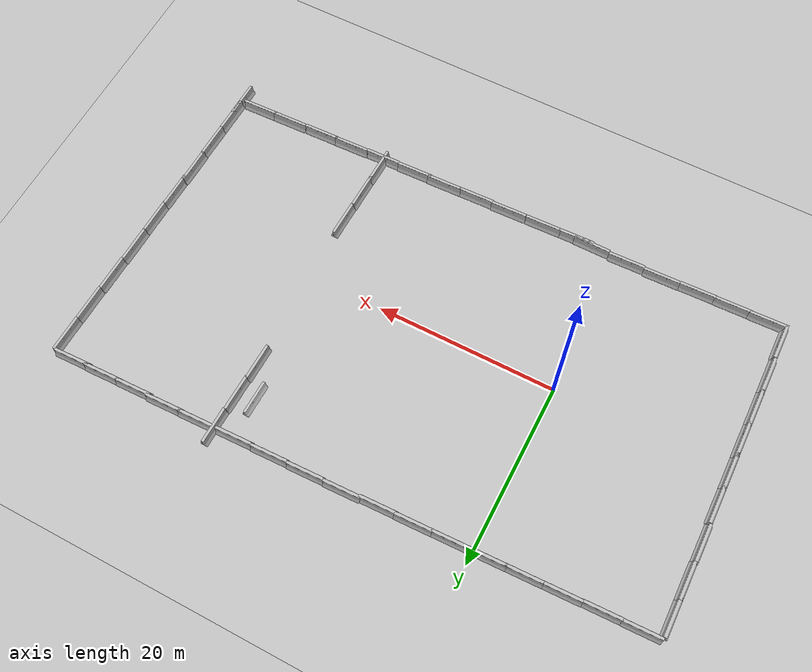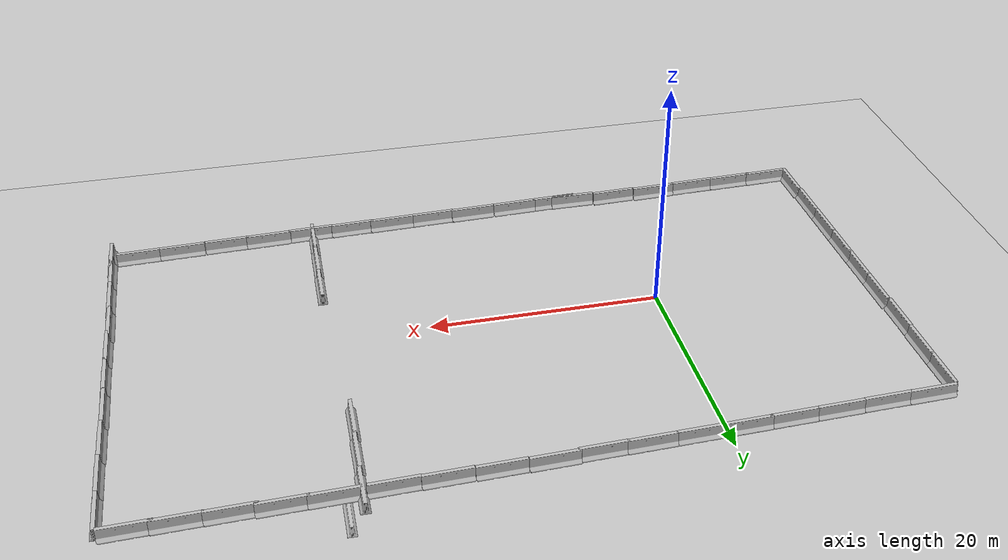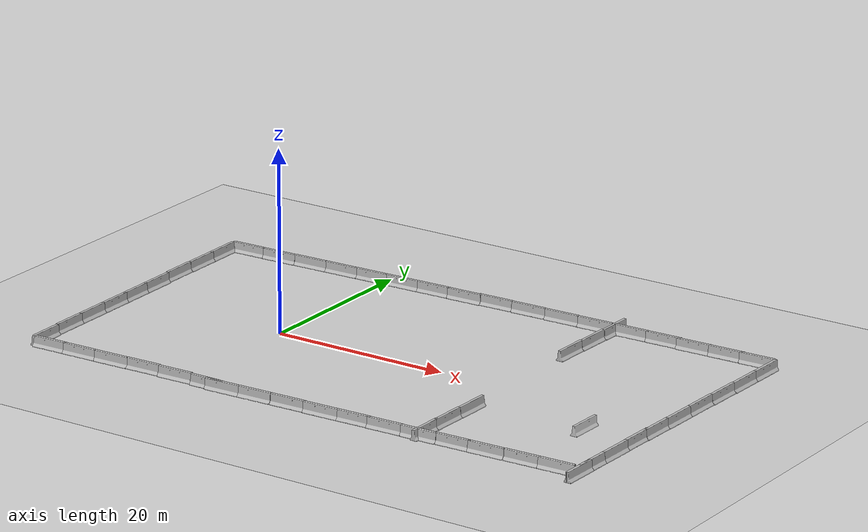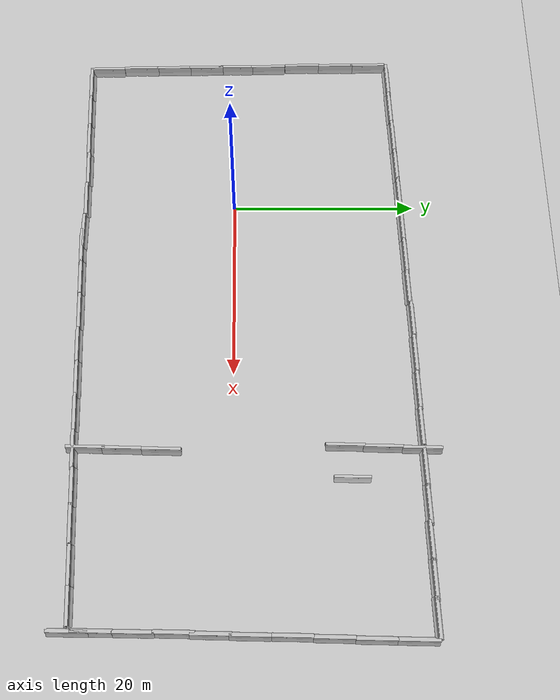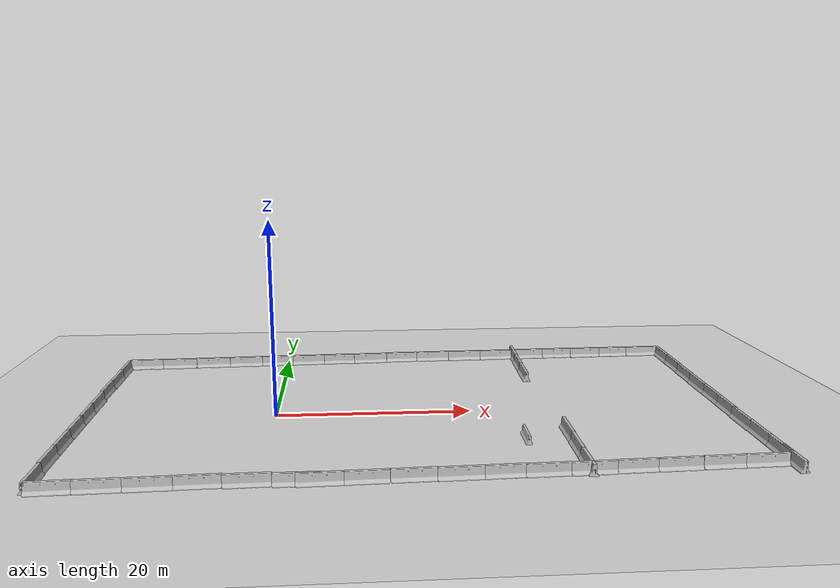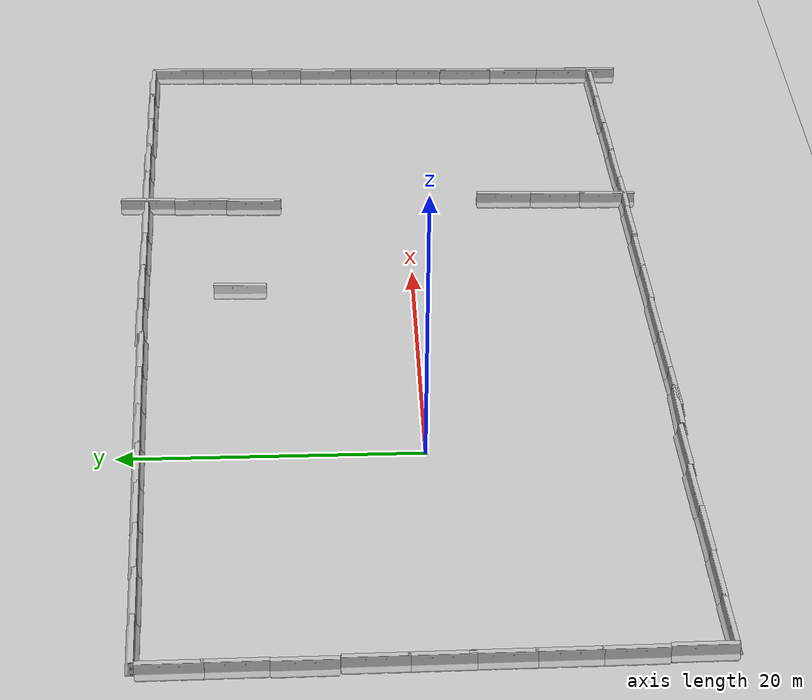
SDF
<sdf version="1.6">
 <world name="default">
  <light name="sun" type="directional">
   <pose>0 0 10 0 -0 0</pose>
   <diffuse>0.8 0.8 0.8 1</diffuse>
   <specular>0.2 0.2 0.2 1</specular>
   <attenuation>
    <range>1000</range>
    <constant>0.9</constant>
    <linear>0.01</linear>
    <quadratic>0.001</quadratic>
   </attenuation>
   <direction>-0.5 0.1 -0.9</direction>
  </light>
  <model name="ground_plane">
   <static>1</static>
   <link name="link">
    <collision name="collision">
     <geometry><plane><normal>0 0 1</normal><size>100 100</size></plane></geometry>
     <surface><friction><ode><mu>100</mu><mu2>50</mu2></ode></friction></surface>
    </collision>
    <visual name="visual">
     <cast_shadows>0</cast_shadows>
     <geometry><plane><normal>0 0 1</normal><size>100 100</size></plane></geometry>
     <material>
      <script><uri>file://media/materials/scripts/gazebo.material</uri><name>Gazebo/Grey</name></script>
     </material>
    </visual>
   </link>
  </model>
  <physics name="default_physics" default="0" type="ode">
   <max_step_size>0.01</max_step_size>
   <real_time_factor>1</real_time_factor>
   <real_time_update_rate>100</real_time_update_rate>
  </physics>
  <gravity>0 0 -9.8</gravity>
  <magnetic_field>6e-06 2.3e-05 -4.2e-05</magnetic_field>
  <atmosphere type="adiabatic"/>
  <scene><ambient>0.4 0.4 0.4 1</ambient><background>0.7 0.7 0.7 1</background><shadows>1</shadows></scene>
  <spherical_coordinates>
   <surface_model>EARTH_WGS84</surface_model>
   <latitude_deg>0</latitude_deg>
   <longitude_deg>0</longitude_deg>
   <elevation>0</elevation>
   <heading_deg>0</heading_deg>
  </spherical_coordinates>
  <model name="jersey_barrier">
   <static>1</static>
   <link name="link">
    <visual name="visual">
     <geometry>
      <mesh><uri>model://jersey_barrier/meshes/jersey_barrier.dae</uri><scale>1 1 1</scale></mesh>
     </geometry>
    </visual>
    <collision name="upright">
     <pose>0 0 0.5715 0 -0 0</pose>
     <geometry><box><size>4.06542 0.3063 1.143</size></box></geometry>
    </collision>
    <collision name="base">
     <pose>0 0 0.032258 0 -0 0</pose>
     <geometry><box><size>4.06542 0.8107 0.064516</size></box></geometry>
    </collision>
    <collision name="base2">
     <pose>0 0 0.1 0 -0 0</pose>
     <geometry><box><size>4.06542 0.65 0.1</size></box></geometry>
    </collision>
    <collision name="base3">
     <pose>0 0 0.2 0 -0 0</pose>
     <geometry><box><size>4.06542 0.5 0.1</size></box></geometry>
    </collision>
    <collision name="left-angle">
     <pose>0 -0.224 0.2401 0.9 -0 0</pose>
     <geometry><box><size>4.06542 0.5 0.064516</size></box></geometry>
    </collision>
    <collision name="right-angle">
     <pose>0 0.224 0.2401 -0.9 0 0</pose>
     <geometry><box><size>4.06542 0.5 0.064516</size></box></geometry>
    </collision>
   </link>
   <pose>-0.913416 -16.6952 0 0 -0 0.033275</pose>
  </model>
  <model name="jersey_barrier_clone">
   <static>1</static>
   <link name="link">
    <visual name="visual">
     <geometry>
      <mesh><uri>model://jersey_barrier/meshes/jersey_barrier.dae</uri><scale>1 1 1</scale></mesh>
     </geometry>
    </visual>
    <collision name="upright">
     <pose>0 0 0.5715 0 -0 0</pose>
     <geometry><box><size>4.06542 0.3063 1.143</size></box></geometry>
    </collision>
    <collision name="base">
     <pose>0 0 0.032258 0 -0 0</pose>
     <geometry><box><size>4.06542 0.8107 0.064516</size></box></geometry>
    </collision>
    <collision name="base2">
     <pose>0 0 0.1 0 -0 0</pose>
     <geometry><box><size>4.06542 0.65 0.1</size></box></geometry>
    </collision>
    <collision name="base3">
     <pose>0 0 0.2 0 -0 0</pose>
     <geometry><box><size>4.06542 0.5 0.1</size></box></geometry>
    </collision>
    <collision name="left-angle">
     <pose>0 -0.224 0.2401 0.9 -0 0</pose>
     <geometry><box><size>4.06542 0.5 0.064516</size></box></geometry>
    </collision>
    <collision name="right-angle">
     <pose>0 0.224 0.2401 -0.9 0 0</pose>
     <geometry><box><size>4.06542 0.5 0.064516</size></box></geometry>
    </collision>
   </link>
   <pose>5.06368 -16.8524 0 0 -0 0.033275</pose>
  </model>
  <model name="jersey_barrier_clone_clone">
   <static>1</static>
   <link name="link">
    <visual name="visual">
     <geometry>
      <mesh><uri>model://jersey_barrier/meshes/jersey_barrier.dae</uri><scale>1 1 1</scale></mesh>
     </geometry>
    </visual>
    <collision name="upright">
     <pose>0 0 0.5715 0 -0 0</pose>
     <geometry><box><size>4.06542 0.3063 1.143</size></box></geometry>
    </collision>
    <collision name="base">
     <pose>0 0 0.032258 0 -0 0</pose>
     <geometry><box><size>4.06542 0.8107 0.064516</size></box></geometry>
    </collision>
    <collision name="base2">
     <pose>0 0 0.1 0 -0 0</pose>
     <geometry><box><size>4.06542 0.65 0.1</size></box></geometry>
    </collision>
    <collision name="base3">
     <pose>0 0 0.2 0 -0 0</pose>
     <geometry><box><size>4.06542 0.5 0.1</size></box></geometry>
    </collision>
    <collision name="left-angle">
     <pose>0 -0.224 0.2401 0.9 -0 0</pose>
     <geometry><box><size>4.06542 0.5 0.064516</size></box></geometry>
    </collision>
    <collision name="right-angle">
     <pose>0 0.224 0.2401 -0.9 0 0</pose>
     <geometry><box><size>4.06542 0.5 0.064516</size></box></geometry>
    </collision>
   </link>
   <pose>-4.93978 -16.7019 0 0 -0 0.033275</pose>
  </model>
  <model name="jersey_barrier_clone_clone_0">
   <static>1</static>
   <link name="link">
    <visual name="visual">
     <geometry>
      <mesh><uri>model://jersey_barrier/meshes/jersey_barrier.dae</uri><scale>1 1 1</scale></mesh>
     </geometry>
    </visual>
    <collision name="upright">
     <pose>0 0 0.5715 0 -0 0</pose>
     <geometry><box><size>4.06542 0.3063 1.143</size></box></geometry>
    </collision>
    <collision name="base">
     <pose>0 0 0.032258 0 -0 0</pose>
     <geometry><box><size>4.06542 0.8107 0.064516</size></box></geometry>
    </collision>
    <collision name="base2">
     <pose>0 0 0.1 0 -0 0</pose>
     <geometry><box><size>4.06542 0.65 0.1</size></box></geometry>
    </collision>
    <collision name="base3">
     <pose>0 0 0.2 0 -0 0</pose>
     <geometry><box><size>4.06542 0.5 0.1</size></box></geometry>
    </collision>
    <collision name="left-angle">
     <pose>0 -0.224 0.2401 0.9 -0 0</pose>
     <geometry><box><size>4.06542 0.5 0.064516</size></box></geometry>
    </collision>
    <collision name="right-angle">
     <pose>0 0.224 0.2401 -0.9 0 0</pose>
     <geometry><box><size>4.06542 0.5 0.064516</size></box></geometry>
    </collision>
   </link>
   <pose>8.87687 -16.7227 0 0 -0 0.033275</pose>
  </model>
  <model name="jersey_barrier_clone_clone_1">
   <static>1</static>
   <link name="link">
    <visual name="visual">
     <geometry>
      <mesh><uri>model://jersey_barrier/meshes/jersey_barrier.dae</uri><scale>1 1 1</scale></mesh>
     </geometry>
    </visual>
    <collision name="upright">
     <pose>0 0 0.5715 0 -0 0</pose>
     <geometry><box><size>4.06542 0.3063 1.143</size></box></geometry>
    </collision>
    <collision name="base">
     <pose>0 0 0.032258 0 -0 0</pose>
     <geometry><box><size>4.06542 0.8107 0.064516</size></box></geometry>
    </collision>
    <collision name="base2">
     <pose>0 0 0.1 0 -0 0</pose>
     <geometry><box><size>4.06542 0.65 0.1</size></box></geometry>
    </collision>
    <collision name="base3">
     <pose>0 0 0.2 0 -0 0</pose>
     <geometry><box><size>4.06542 0.5 0.1</size></box></geometry>
    </collision>
    <collision name="left-angle">
     <pose>0 -0.224 0.2401 0.9 -0 0</pose>
     <geometry><box><size>4.06542 0.5 0.064516</size></box></geometry>
    </collision>
    <collision name="right-angle">
     <pose>0 0.224 0.2401 -0.9 0 0</pose>
     <geometry><box><size>4.06542 0.5 0.064516</size></box></geometry>
    </collision>
   </link>
   <pose>12.9707 -16.5908 0 0 -0 0.033275</pose>
  </model>
  <model name="jersey_barrier_clone_clone_2">
   <static>1</static>
   <link name="link">
    <visual name="visual">
     <geometry>
      <mesh><uri>model://jersey_barrier/meshes/jersey_barrier.dae</uri><scale>1 1 1</scale></mesh>
     </geometry>
    </visual>
    <collision name="upright">
     <pose>0 0 0.5715 0 -0 0</pose>
     <geometry><box><size>4.06542 0.3063 1.143</size></box></geometry>
    </collision>
    <collision name="base">
     <pose>0 0 0.032258 0 -0 0</pose>
     <geometry><box><size>4.06542 0.8107 0.064516</size></box></geometry>
    </collision>
    <collision name="base2">
     <pose>0 0 0.1 0 -0 0</pose>
     <geometry><box><size>4.06542 0.65 0.1</size></box></geometry>
    </collision>
    <collision name="base3">
     <pose>0 0 0.2 0 -0 0</pose>
     <geometry><box><size>4.06542 0.5 0.1</size></box></geometry>
    </collision>
    <collision name="left-angle">
     <pose>0 -0.224 0.2401 0.9 -0 0</pose>
     <geometry><box><size>4.06542 0.5 0.064516</size></box></geometry>
    </collision>
    <collision name="right-angle">
     <pose>0 0.224 0.2401 -0.9 0 0</pose>
     <geometry><box><size>4.06542 0.5 0.064516</size></box></geometry>
    </collision>
   </link>
   <pose>16.8898 -16.5319 0 0 -0 0.033275</pose>
  </model>
  <model name="jersey_barrier_clone_clone_3">
   <static>1</static>
   <link name="link">
    <visual name="visual">
     <geometry>
      <mesh><uri>model://jersey_barrier/meshes/jersey_barrier.dae</uri><scale>1 1 1</scale></mesh>
     </geometry>
    </visual>
    <collision name="upright">
     <pose>0 0 0.5715 0 -0 0</pose>
     <geometry><box><size>4.06542 0.3063 1.143</size></box></geometry>
    </collision>
    <collision name="base">
     <pose>0 0 0.032258 0 -0 0</pose>
     <geometry><box><size>4.06542 0.8107 0.064516</size></box></geometry>
    </collision>
    <collision name="base2">
     <pose>0 0 0.1 0 -0 0</pose>
     <geometry><box><size>4.06542 0.65 0.1</size></box></geometry>
    </collision>
    <collision name="base3">
     <pose>0 0 0.2 0 -0 0</pose>
     <geometry><box><size>4.06542 0.5 0.1</size></box></geometry>
    </collision>
    <collision name="left-angle">
     <pose>0 -0.224 0.2401 0.9 -0 0</pose>
     <geometry><box><size>4.06542 0.5 0.064516</size></box></geometry>
    </collision>
    <collision name="right-angle">
     <pose>0 0.224 0.2401 -0.9 0 0</pose>
     <geometry><box><size>4.06542 0.5 0.064516</size></box></geometry>
    </collision>
   </link>
   <pose>20.7541 -16.3983 0 0 -0 0.033275</pose>
  </model>
  <model name="jersey_barrier_clone_clone_clone">
   <static>1</static>
   <link name="link">
    <visual name="visual">
     <geometry>
      <mesh><uri>model://jersey_barrier/meshes/jersey_barrier.dae</uri><scale>1 1 1</scale></mesh>
     </geometry>
    </visual>
    <collision name="upright">
     <pose>0 0 0.5715 0 -0 0</pose>
     <geometry><box><size>4.06542 0.3063 1.143</size></box></geometry>
    </collision>
    <collision name="base">
     <pose>0 0 0.032258 0 -0 0</pose>
     <geometry><box><size>4.06542 0.8107 0.064516</size></box></geometry>
    </collision>
    <collision name="base2">
     <pose>0 0 0.1 0 -0 0</pose>
     <geometry><box><size>4.06542 0.65 0.1</size></box></geometry>
    </collision>
    <collision name="base3">
     <pose>0 0 0.2 0 -0 0</pose>
     <geometry><box><size>4.06542 0.5 0.1</size></box></geometry>
    </collision>
    <collision name="left-angle">
     <pose>0 -0.224 0.2401 0.9 -0 0</pose>
     <geometry><box><size>4.06542 0.5 0.064516</size></box></geometry>
    </collision>
    <collision name="right-angle">
     <pose>0 0.224 0.2401 -0.9 0 0</pose>
     <geometry><box><size>4.06542 0.5 0.064516</size></box></geometry>
    </collision>
   </link>
   <pose>24.4141 -16.3295 0 0 -0 0.033275</pose>
  </model>
  <model name="jersey_barrier_clone_clone_clone_0">
   <static>1</static>
   <link name="link">
    <visual name="visual">
     <geometry>
      <mesh><uri>model://jersey_barrier/meshes/jersey_barrier.dae</uri><scale>1 1 1</scale></mesh>
     </geometry>
    </visual>
    <collision name="upright">
     <pose>0 0 0.5715 0 -0 0</pose>
     <geometry><box><size>4.06542 0.3063 1.143</size></box></geometry>
    </collision>
    <collision name="base">
     <pose>0 0 0.032258 0 -0 0</pose>
     <geometry><box><size>4.06542 0.8107 0.064516</size></box></geometry>
    </collision>
    <collision name="base2">
     <pose>0 0 0.1 0 -0 0</pose>
     <geometry><box><size>4.06542 0.65 0.1</size></box></geometry>
    </collision>
    <collision name="base3">
     <pose>0 0 0.2 0 -0 0</pose>
     <geometry><box><size>4.06542 0.5 0.1</size></box></geometry>
    </collision>
    <collision name="left-angle">
     <pose>0 -0.224 0.2401 0.9 -0 0</pose>
     <geometry><box><size>4.06542 0.5 0.064516</size></box></geometry>
    </collision>
    <collision name="right-angle">
     <pose>0 0.224 0.2401 -0.9 0 0</pose>
     <geometry><box><size>4.06542 0.5 0.064516</size></box></geometry>
    </collision>
   </link>
   <pose>-8.88852 -16.868 0 0 -0 0.033275</pose>
  </model>
  <model name="jersey_barrier_clone_clone_clone_2">
   <static>1</static>
   <link name="link">
    <visual name="visual">
     <geometry>
      <mesh><uri>model://jersey_barrier/meshes/jersey_barrier.dae</uri><scale>1 1 1</scale></mesh>
     </geometry>
    </visual>
    <collision name="upright">
     <pose>0 0 0.5715 0 -0 0</pose>
     <geometry><box><size>4.06542 0.3063 1.143</size></box></geometry>
    </collision>
    <collision name="base">
     <pose>0 0 0.032258 0 -0 0</pose>
     <geometry><box><size>4.06542 0.8107 0.064516</size></box></geometry>
    </collision>
    <collision name="base2">
     <pose>0 0 0.1 0 -0 0</pose>
     <geometry><box><size>4.06542 0.65 0.1</size></box></geometry>
    </collision>
    <collision name="base3">
     <pose>0 0 0.2 0 -0 0</pose>
     <geometry><box><size>4.06542 0.5 0.1</size></box></geometry>
    </collision>
    <collision name="left-angle">
     <pose>0 -0.224 0.2401 0.9 -0 0</pose>
     <geometry><box><size>4.06542 0.5 0.064516</size></box></geometry>
    </collision>
    <collision name="right-angle">
     <pose>0 0.224 0.2401 -0.9 0 0</pose>
     <geometry><box><size>4.06542 0.5 0.064516</size></box></geometry>
    </collision>
   </link>
   <pose>-12.8673 -16.9656 0 0 -0 0.033275</pose>
  </model>
  <model name="jersey_barrier_clone_clone_clone_3_clone">
   <static>1</static>
   <link name="link">
    <visual name="visual">
     <geometry>
      <mesh><uri>model://jersey_barrier/meshes/jersey_barrier.dae</uri><scale>1 1 1</scale></mesh>
     </geometry>
    </visual>
    <collision name="upright">
     <pose>0 0 0.5715 0 -0 0</pose>
     <geometry><box><size>4.06542 0.3063 1.143</size></box></geometry>
    </collision>
    <collision name="base">
     <pose>0 0 0.032258 0 -0 0</pose>
     <geometry><box><size>4.06542 0.8107 0.064516</size></box></geometry>
    </collision>
    <collision name="base2">
     <pose>0 0 0.1 0 -0 0</pose>
     <geometry><box><size>4.06542 0.65 0.1</size></box></geometry>
    </collision>
    <collision name="base3">
     <pose>0 0 0.2 0 -0 0</pose>
     <geometry><box><size>4.06542 0.5 0.1</size></box></geometry>
    </collision>
    <collision name="left-angle">
     <pose>0 -0.224 0.2401 0.9 -0 0</pose>
     <geometry><box><size>4.06542 0.5 0.064516</size></box></geometry>
    </collision>
    <collision name="right-angle">
     <pose>0 0.224 0.2401 -0.9 0 0</pose>
     <geometry><box><size>4.06542 0.5 0.064516</size></box></geometry>
    </collision>
   </link>
   <pose>28.2276 -14.9648 0 0 0 -1.5926</pose>
  </model>
  <model name="jersey_barrier_clone_clone_clone_3_clone_clone">
   <static>1</static>
   <link name="link">
    <visual name="visual">
     <geometry>
      <mesh><uri>model://jersey_barrier/meshes/jersey_barrier.dae</uri><scale>1 1 1</scale></mesh>
     </geometry>
    </visual>
    <collision name="upright">
     <pose>0 0 0.5715 0 -0 0</pose>
     <geometry><box><size>4.06542 0.3063 1.143</size></box></geometry>
    </collision>
    <collision name="base">
     <pose>0 0 0.032258 0 -0 0</pose>
     <geometry><box><size>4.06542 0.8107 0.064516</size></box></geometry>
    </collision>
    <collision name="base2">
     <pose>0 0 0.1 0 -0 0</pose>
     <geometry><box><size>4.06542 0.65 0.1</size></box></geometry>
    </collision>
    <collision name="base3">
     <pose>0 0 0.2 0 -0 0</pose>
     <geometry><box><size>4.06542 0.5 0.1</size></box></geometry>
    </collision>
    <collision name="left-angle">
     <pose>0 -0.224 0.2401 0.9 -0 0</pose>
     <geometry><box><size>4.06542 0.5 0.064516</size></box></geometry>
    </collision>
    <collision name="right-angle">
     <pose>0 0.224 0.2401 -0.9 0 0</pose>
     <geometry><box><size>4.06542 0.5 0.064516</size></box></geometry>
    </collision>
   </link>
   <pose>28.3372 -11.2824 0 0 0 -1.5926</pose>
  </model>
  <model name="jersey_barrier_clone_clone_clone_3_clone_clone_0">
   <static>1</static>
   <link name="link">
    <visual name="visual">
     <geometry>
      <mesh><uri>model://jersey_barrier/meshes/jersey_barrier.dae</uri><scale>1 1 1</scale></mesh>
     </geometry>
    </visual>
    <collision name="upright">
     <pose>0 0 0.5715 0 -0 0</pose>
     <geometry><box><size>4.06542 0.3063 1.143</size></box></geometry>
    </collision>
    <collision name="base">
     <pose>0 0 0.032258 0 -0 0</pose>
     <geometry><box><size>4.06542 0.8107 0.064516</size></box></geometry>
    </collision>
    <collision name="base2">
     <pose>0 0 0.1 0 -0 0</pose>
     <geometry><box><size>4.06542 0.65 0.1</size></box></geometry>
    </collision>
    <collision name="base3">
     <pose>0 0 0.2 0 -0 0</pose>
     <geometry><box><size>4.06542 0.5 0.1</size></box></geometry>
    </collision>
    <collision name="left-angle">
     <pose>0 -0.224 0.2401 0.9 -0 0</pose>
     <geometry><box><size>4.06542 0.5 0.064516</size></box></geometry>
    </collision>
    <collision name="right-angle">
     <pose>0 0.224 0.2401 -0.9 0 0</pose>
     <geometry><box><size>4.06542 0.5 0.064516</size></box></geometry>
    </collision>
   </link>
   <pose>28.4632 -7.24807 0 0 0 -1.5926</pose>
  </model>
  <model name="jersey_barrier_clone_clone_clone_clone">
   <static>1</static>
   <link name="link">
    <visual name="visual">
     <geometry>
      <mesh><uri>model://jersey_barrier/meshes/jersey_barrier.dae</uri><scale>1 1 1</scale></mesh>
     </geometry>
    </visual>
    <collision name="upright">
     <pose>0 0 0.5715 0 -0 0</pose>
     <geometry><box><size>4.06542 0.3063 1.143</size></box></geometry>
    </collision>
    <collision name="base">
     <pose>0 0 0.032258 0 -0 0</pose>
     <geometry><box><size>4.06542 0.8107 0.064516</size></box></geometry>
    </collision>
    <collision name="base2">
     <pose>0 0 0.1 0 -0 0</pose>
     <geometry><box><size>4.06542 0.65 0.1</size></box></geometry>
    </collision>
    <collision name="base3">
     <pose>0 0 0.2 0 -0 0</pose>
     <geometry><box><size>4.06542 0.5 0.1</size></box></geometry>
    </collision>
    <collision name="left-angle">
     <pose>0 -0.224 0.2401 0.9 -0 0</pose>
     <geometry><box><size>4.06542 0.5 0.064516</size></box></geometry>
    </collision>
    <collision name="right-angle">
     <pose>0 0.224 0.2401 -0.9 0 0</pose>
     <geometry><box><size>4.06542 0.5 0.064516</size></box></geometry>
    </collision>
   </link>
   <pose>28.3606 -16.2557 0 0 -0 0.033275</pose>
  </model>
  <model name="jersey_barrier_clone_clone_clone_3_clone_clone_1">
   <static>1</static>
   <link name="link">
    <visual name="visual">
     <geometry>
      <mesh><uri>model://jersey_barrier/meshes/jersey_barrier.dae</uri><scale>1 1 1</scale></mesh>
     </geometry>
    </visual>
    <collision name="upright">
     <pose>0 0 0.5715 0 -0 0</pose>
     <geometry><box><size>4.06542 0.3063 1.143</size></box></geometry>
    </collision>
    <collision name="base">
     <pose>0 0 0.032258 0 -0 0</pose>
     <geometry><box><size>4.06542 0.8107 0.064516</size></box></geometry>
    </collision>
    <collision name="base2">
     <pose>0 0 0.1 0 -0 0</pose>
     <geometry><box><size>4.06542 0.65 0.1</size></box></geometry>
    </collision>
    <collision name="base3">
     <pose>0 0 0.2 0 -0 0</pose>
     <geometry><box><size>4.06542 0.5 0.1</size></box></geometry>
    </collision>
    <collision name="left-angle">
     <pose>0 -0.224 0.2401 0.9 -0 0</pose>
     <geometry><box><size>4.06542 0.5 0.064516</size></box></geometry>
    </collision>
    <collision name="right-angle">
     <pose>0 0.224 0.2401 -0.9 0 0</pose>
     <geometry><box><size>4.06542 0.5 0.064516</size></box></geometry>
    </collision>
   </link>
   <pose>28.2436 15.3088 0 0 0 -1.5926</pose>
  </model>
  <model name="jersey_barrier_clone_clone_clone_3_clone_clone_2">
   <static>1</static>
   <link name="link">
    <visual name="visual">
     <geometry>
      <mesh><uri>model://jersey_barrier/meshes/jersey_barrier.dae</uri><scale>1 1 1</scale></mesh>
     </geometry>
    </visual>
    <collision name="upright">
     <pose>0 0 0.5715 0 -0 0</pose>
     <geometry><box><size>4.06542 0.3063 1.143</size></box></geometry>
    </collision>
    <collision name="base">
     <pose>0 0 0.032258 0 -0 0</pose>
     <geometry><box><size>4.06542 0.8107 0.064516</size></box></geometry>
    </collision>
    <collision name="base2">
     <pose>0 0 0.1 0 -0 0</pose>
     <geometry><box><size>4.06542 0.65 0.1</size></box></geometry>
    </collision>
    <collision name="base3">
     <pose>0 0 0.2 0 -0 0</pose>
     <geometry><box><size>4.06542 0.5 0.1</size></box></geometry>
    </collision>
    <collision name="left-angle">
     <pose>0 -0.224 0.2401 0.9 -0 0</pose>
     <geometry><box><size>4.06542 0.5 0.064516</size></box></geometry>
    </collision>
    <collision name="right-angle">
     <pose>0 0.224 0.2401 -0.9 0 0</pose>
     <geometry><box><size>4.06542 0.5 0.064516</size></box></geometry>
    </collision>
   </link>
   <pose>29.0417 12.8143 -8.43284 0 0 -1.5926</pose>
  </model>
  <model name="jersey_barrier_clone_clone_clone_3_clone_clone_3">
   <static>1</static>
   <link name="link">
    <visual name="visual">
     <geometry>
      <mesh><uri>model://jersey_barrier/meshes/jersey_barrier.dae</uri><scale>1 1 1</scale></mesh>
     </geometry>
    </visual>
    <collision name="upright">
     <pose>0 0 0.5715 0 -0 0</pose>
     <geometry><box><size>4.06542 0.3063 1.143</size></box></geometry>
    </collision>
    <collision name="base">
     <pose>0 0 0.032258 0 -0 0</pose>
     <geometry><box><size>4.06542 0.8107 0.064516</size></box></geometry>
    </collision>
    <collision name="base2">
     <pose>0 0 0.1 0 -0 0</pose>
     <geometry><box><size>4.06542 0.65 0.1</size></box></geometry>
    </collision>
    <collision name="base3">
     <pose>0 0 0.2 0 -0 0</pose>
     <geometry><box><size>4.06542 0.5 0.1</size></box></geometry>
    </collision>
    <collision name="left-angle">
     <pose>0 -0.224 0.2401 0.9 -0 0</pose>
     <geometry><box><size>4.06542 0.5 0.064516</size></box></geometry>
    </collision>
    <collision name="right-angle">
     <pose>0 0.224 0.2401 -0.9 0 0</pose>
     <geometry><box><size>4.06542 0.5 0.064516</size></box></geometry>
    </collision>
   </link>
   <pose>28.0855 11.4464 0 0 0 -1.5926</pose>
  </model>
  <model name="jersey_barrier_clone_clone_clone_3_clone_clone_1_clone">
   <static>1</static>
   <link name="link">
    <visual name="visual">
     <geometry>
      <mesh><uri>model://jersey_barrier/meshes/jersey_barrier.dae</uri><scale>1 1 1</scale></mesh>
     </geometry>
    </visual>
    <collision name="upright">
     <pose>0 0 0.5715 0 -0 0</pose>
     <geometry><box><size>4.06542 0.3063 1.143</size></box></geometry>
    </collision>
    <collision name="base">
     <pose>0 0 0.032258 0 -0 0</pose>
     <geometry><box><size>4.06542 0.8107 0.064516</size></box></geometry>
    </collision>
    <collision name="base2">
     <pose>0 0 0.1 0 -0 0</pose>
     <geometry><box><size>4.06542 0.65 0.1</size></box></geometry>
    </collision>
    <collision name="base3">
     <pose>0 0 0.2 0 -0 0</pose>
     <geometry><box><size>4.06542 0.5 0.1</size></box></geometry>
    </collision>
    <collision name="left-angle">
     <pose>0 -0.224 0.2401 0.9 -0 0</pose>
     <geometry><box><size>4.06542 0.5 0.064516</size></box></geometry>
    </collision>
    <collision name="right-angle">
     <pose>0 0.224 0.2401 -0.9 0 0</pose>
     <geometry><box><size>4.06542 0.5 0.064516</size></box></geometry>
    </collision>
   </link>
   <pose>28.4083 19.2885 0 0 0 -1.5926</pose>
  </model>
  <model name="jersey_barrier_clone_clone_clone_clone_0">
   <static>1</static>
   <link name="link">
    <visual name="visual">
     <geometry>
      <mesh><uri>model://jersey_barrier/meshes/jersey_barrier.dae</uri><scale>1 1 1</scale></mesh>
     </geometry>
    </visual>
    <collision name="upright">
     <pose>0 0 0.5715 0 -0 0</pose>
     <geometry><box><size>4.06542 0.3063 1.143</size></box></geometry>
    </collision>
    <collision name="base">
     <pose>0 0 0.032258 0 -0 0</pose>
     <geometry><box><size>4.06542 0.8107 0.064516</size></box></geometry>
    </collision>
    <collision name="base2">
     <pose>0 0 0.1 0 -0 0</pose>
     <geometry><box><size>4.06542 0.65 0.1</size></box></geometry>
    </collision>
    <collision name="base3">
     <pose>0 0 0.2 0 -0 0</pose>
     <geometry><box><size>4.06542 0.5 0.1</size></box></geometry>
    </collision>
    <collision name="left-angle">
     <pose>0 -0.224 0.2401 0.9 -0 0</pose>
     <geometry><box><size>4.06542 0.5 0.064516</size></box></geometry>
    </collision>
    <collision name="right-angle">
     <pose>0 0.224 0.2401 -0.9 0 0</pose>
     <geometry><box><size>4.06542 0.5 0.064516</size></box></geometry>
    </collision>
   </link>
   <pose>26.0844 19.3245 0 0 -0 0.033275</pose>
  </model>
  <model name="jersey_barrier_clone_clone_clone_clone_0_clone">
   <static>1</static>
   <link name="link">
    <visual name="visual">
     <geometry>
      <mesh><uri>model://jersey_barrier/meshes/jersey_barrier.dae</uri><scale>1 1 1</scale></mesh>
     </geometry>
    </visual>
    <collision name="upright">
     <pose>0 0 0.5715 0 -0 0</pose>
     <geometry><box><size>4.06542 0.3063 1.143</size></box></geometry>
    </collision>
    <collision name="base">
     <pose>0 0 0.032258 0 -0 0</pose>
     <geometry><box><size>4.06542 0.8107 0.064516</size></box></geometry>
    </collision>
    <collision name="base2">
     <pose>0 0 0.1 0 -0 0</pose>
     <geometry><box><size>4.06542 0.65 0.1</size></box></geometry>
    </collision>
    <collision name="base3">
     <pose>0 0 0.2 0 -0 0</pose>
     <geometry><box><size>4.06542 0.5 0.1</size></box></geometry>
    </collision>
    <collision name="left-angle">
     <pose>0 -0.224 0.2401 0.9 -0 0</pose>
     <geometry><box><size>4.06542 0.5 0.064516</size></box></geometry>
    </collision>
    <collision name="right-angle">
     <pose>0 0.224 0.2401 -0.9 0 0</pose>
     <geometry><box><size>4.06542 0.5 0.064516</size></box></geometry>
    </collision>
   </link>
   <pose>22.068 19.2501 0 0 -0 0.033275</pose>
  </model>
  <model name="jersey_barrier_clone_clone_clone_clone_0_clone_0">
   <static>1</static>
   <link name="link">
    <visual name="visual">
     <geometry>
      <mesh><uri>model://jersey_barrier/meshes/jersey_barrier.dae</uri><scale>1 1 1</scale></mesh>
     </geometry>
    </visual>
    <collision name="upright">
     <pose>0 0 0.5715 0 -0 0</pose>
     <geometry><box><size>4.06542 0.3063 1.143</size></box></geometry>
    </collision>
    <collision name="base">
     <pose>0 0 0.032258 0 -0 0</pose>
     <geometry><box><size>4.06542 0.8107 0.064516</size></box></geometry>
    </collision>
    <collision name="base2">
     <pose>0 0 0.1 0 -0 0</pose>
     <geometry><box><size>4.06542 0.65 0.1</size></box></geometry>
    </collision>
    <collision name="base3">
     <pose>0 0 0.2 0 -0 0</pose>
     <geometry><box><size>4.06542 0.5 0.1</size></box></geometry>
    </collision>
    <collision name="left-angle">
     <pose>0 -0.224 0.2401 0.9 -0 0</pose>
     <geometry><box><size>4.06542 0.5 0.064516</size></box></geometry>
    </collision>
    <collision name="right-angle">
     <pose>0 0.224 0.2401 -0.9 0 0</pose>
     <geometry><box><size>4.06542 0.5 0.064516</size></box></geometry>
    </collision>
   </link>
   <pose>18.0097 19.1749 0 0 -0 0.033275</pose>
  </model>
  <model name="jersey_barrier_clone_clone_clone_clone_0_clone_0_clone">
   <static>1</static>
   <link name="link">
    <visual name="visual">
     <geometry>
      <mesh><uri>model://jersey_barrier/meshes/jersey_barrier.dae</uri><scale>1 1 1</scale></mesh>
     </geometry>
    </visual>
    <collision name="upright">
     <pose>0 0 0.5715 0 -0 0</pose>
     <geometry><box><size>4.06542 0.3063 1.143</size></box></geometry>
    </collision>
    <collision name="base">
     <pose>0 0 0.032258 0 -0 0</pose>
     <geometry><box><size>4.06542 0.8107 0.064516</size></box></geometry>
    </collision>
    <collision name="base2">
     <pose>0 0 0.1 0 -0 0</pose>
     <geometry><box><size>4.06542 0.65 0.1</size></box></geometry>
    </collision>
    <collision name="base3">
     <pose>0 0 0.2 0 -0 0</pose>
     <geometry><box><size>4.06542 0.5 0.1</size></box></geometry>
    </collision>
    <collision name="left-angle">
     <pose>0 -0.224 0.2401 0.9 -0 0</pose>
     <geometry><box><size>4.06542 0.5 0.064516</size></box></geometry>
    </collision>
    <collision name="right-angle">
     <pose>0 0.224 0.2401 -0.9 0 0</pose>
     <geometry><box><size>4.06542 0.5 0.064516</size></box></geometry>
    </collision>
   </link>
   <pose>13.949 19.1026 0 0 -0 0.033275</pose>
  </model>
  <model name="jersey_barrier_clone_clone_clone_clone_0_clone_0_clone_clone">
   <static>1</static>
   <link name="link">
    <visual name="visual">
     <geometry>
      <mesh><uri>model://jersey_barrier/meshes/jersey_barrier.dae</uri><scale>1 1 1</scale></mesh>
     </geometry>
    </visual>
    <collision name="upright">
     <pose>0 0 0.5715 0 -0 0</pose>
     <geometry><box><size>4.06542 0.3063 1.143</size></box></geometry>
    </collision>
    <collision name="base">
     <pose>0 0 0.032258 0 -0 0</pose>
     <geometry><box><size>4.06542 0.8107 0.064516</size></box></geometry>
    </collision>
    <collision name="base2">
     <pose>0 0 0.1 0 -0 0</pose>
     <geometry><box><size>4.06542 0.65 0.1</size></box></geometry>
    </collision>
    <collision name="base3">
     <pose>0 0 0.2 0 -0 0</pose>
     <geometry><box><size>4.06542 0.5 0.1</size></box></geometry>
    </collision>
    <collision name="left-angle">
     <pose>0 -0.224 0.2401 0.9 -0 0</pose>
     <geometry><box><size>4.06542 0.5 0.064516</size></box></geometry>
    </collision>
    <collision name="right-angle">
     <pose>0 0.224 0.2401 -0.9 0 0</pose>
     <geometry><box><size>4.06542 0.5 0.064516</size></box></geometry>
    </collision>
   </link>
   <pose>10.1358 18.8674 0 0 -0 0.033275</pose>
  </model>
  <model name="jersey_barrier_clone_clone_clone_clone_0_clone_0_clone_clone_0">
   <static>1</static>
   <link name="link">
    <visual name="visual">
     <geometry>
      <mesh><uri>model://jersey_barrier/meshes/jersey_barrier.dae</uri><scale>1 1 1</scale></mesh>
     </geometry>
    </visual>
    <collision name="upright">
     <pose>0 0 0.5715 0 -0 0</pose>
     <geometry><box><size>4.06542 0.3063 1.143</size></box></geometry>
    </collision>
    <collision name="base">
     <pose>0 0 0.032258 0 -0 0</pose>
     <geometry><box><size>4.06542 0.8107 0.064516</size></box></geometry>
    </collision>
    <collision name="base2">
     <pose>0 0 0.1 0 -0 0</pose>
     <geometry><box><size>4.06542 0.65 0.1</size></box></geometry>
    </collision>
    <collision name="base3">
     <pose>0 0 0.2 0 -0 0</pose>
     <geometry><box><size>4.06542 0.5 0.1</size></box></geometry>
    </collision>
    <collision name="left-angle">
     <pose>0 -0.224 0.2401 0.9 -0 0</pose>
     <geometry><box><size>4.06542 0.5 0.064516</size></box></geometry>
    </collision>
    <collision name="right-angle">
     <pose>0 0.224 0.2401 -0.9 0 0</pose>
     <geometry><box><size>4.06542 0.5 0.064516</size></box></geometry>
    </collision>
   </link>
   <pose>6.27406 18.7774 0 0 -0 0.033275</pose>
  </model>
  <model name="jersey_barrier_clone_clone_clone_clone_0_clone_0_clone_clone_1">
   <static>1</static>
   <link name="link">
    <visual name="visual">
     <geometry>
      <mesh><uri>model://jersey_barrier/meshes/jersey_barrier.dae</uri><scale>1 1 1</scale></mesh>
     </geometry>
    </visual>
    <collision name="upright">
     <pose>0 0 0.5715 0 -0 0</pose>
     <geometry><box><size>4.06542 0.3063 1.143</size></box></geometry>
    </collision>
    <collision name="base">
     <pose>0 0 0.032258 0 -0 0</pose>
     <geometry><box><size>4.06542 0.8107 0.064516</size></box></geometry>
    </collision>
    <collision name="base2">
     <pose>0 0 0.1 0 -0 0</pose>
     <geometry><box><size>4.06542 0.65 0.1</size></box></geometry>
    </collision>
    <collision name="base3">
     <pose>0 0 0.2 0 -0 0</pose>
     <geometry><box><size>4.06542 0.5 0.1</size></box></geometry>
    </collision>
    <collision name="left-angle">
     <pose>0 -0.224 0.2401 0.9 -0 0</pose>
     <geometry><box><size>4.06542 0.5 0.064516</size></box></geometry>
    </collision>
    <collision name="right-angle">
     <pose>0 0.224 0.2401 -0.9 0 0</pose>
     <geometry><box><size>4.06542 0.5 0.064516</size></box></geometry>
    </collision>
   </link>
   <pose>2.36253 18.639 0 0 -0 0.033275</pose>
  </model>
  <model name="jersey_barrier_clone_clone_clone_clone_0_clone_0_clone_clone_2">
   <static>1</static>
   <link name="link">
    <visual name="visual">
     <geometry>
      <mesh><uri>model://jersey_barrier/meshes/jersey_barrier.dae</uri><scale>1 1 1</scale></mesh>
     </geometry>
    </visual>
    <collision name="upright">
     <pose>0 0 0.5715 0 -0 0</pose>
     <geometry><box><size>4.06542 0.3063 1.143</size></box></geometry>
    </collision>
    <collision name="base">
     <pose>0 0 0.032258 0 -0 0</pose>
     <geometry><box><size>4.06542 0.8107 0.064516</size></box></geometry>
    </collision>
    <collision name="base2">
     <pose>0 0 0.1 0 -0 0</pose>
     <geometry><box><size>4.06542 0.65 0.1</size></box></geometry>
    </collision>
    <collision name="base3">
     <pose>0 0 0.2 0 -0 0</pose>
     <geometry><box><size>4.06542 0.5 0.1</size></box></geometry>
    </collision>
    <collision name="left-angle">
     <pose>0 -0.224 0.2401 0.9 -0 0</pose>
     <geometry><box><size>4.06542 0.5 0.064516</size></box></geometry>
    </collision>
    <collision name="right-angle">
     <pose>0 0.224 0.2401 -0.9 0 0</pose>
     <geometry><box><size>4.06542 0.5 0.064516</size></box></geometry>
    </collision>
   </link>
   <pose>-1.50152 18.5003 0 0 -0 0.033275</pose>
  </model>
  <model name="jersey_barrier_clone_clone_clone_clone_0_clone_0_clone_clone_3">
   <static>1</static>
   <link name="link">
    <visual name="visual">
     <geometry>
      <mesh><uri>model://jersey_barrier/meshes/jersey_barrier.dae</uri><scale>1 1 1</scale></mesh>
     </geometry>
    </visual>
    <collision name="upright">
     <pose>0 0 0.5715 0 -0 0</pose>
     <geometry><box><size>4.06542 0.3063 1.143</size></box></geometry>
    </collision>
    <collision name="base">
     <pose>0 0 0.032258 0 -0 0</pose>
     <geometry><box><size>4.06542 0.8107 0.064516</size></box></geometry>
    </collision>
    <collision name="base2">
     <pose>0 0 0.1 0 -0 0</pose>
     <geometry><box><size>4.06542 0.65 0.1</size></box></geometry>
    </collision>
    <collision name="base3">
     <pose>0 0 0.2 0 -0 0</pose>
     <geometry><box><size>4.06542 0.5 0.1</size></box></geometry>
    </collision>
    <collision name="left-angle">
     <pose>0 -0.224 0.2401 0.9 -0 0</pose>
     <geometry><box><size>4.06542 0.5 0.064516</size></box></geometry>
    </collision>
    <collision name="right-angle">
     <pose>0 0.224 0.2401 -0.9 0 0</pose>
     <geometry><box><size>4.06542 0.5 0.064516</size></box></geometry>
    </collision>
   </link>
   <pose>-5.27021 18.3618 0 0 -0 0.033275</pose>
  </model>
  <model name="jersey_barrier_clone_clone_clone_clone_0_clone_0_clone_clone_4">
   <static>1</static>
   <link name="link">
    <visual name="visual">
     <geometry>
      <mesh><uri>model://jersey_barrier/meshes/jersey_barrier.dae</uri><scale>1 1 1</scale></mesh>
     </geometry>
    </visual>
    <collision name="upright">
     <pose>0 0 0.5715 0 -0 0</pose>
     <geometry><box><size>4.06542 0.3063 1.143</size></box></geometry>
    </collision>
    <collision name="base">
     <pose>0 0 0.032258 0 -0 0</pose>
     <geometry><box><size>4.06542 0.8107 0.064516</size></box></geometry>
    </collision>
    <collision name="base2">
     <pose>0 0 0.1 0 -0 0</pose>
     <geometry><box><size>4.06542 0.65 0.1</size></box></geometry>
    </collision>
    <collision name="base3">
     <pose>0 0 0.2 0 -0 0</pose>
     <geometry><box><size>4.06542 0.5 0.1</size></box></geometry>
    </collision>
    <collision name="left-angle">
     <pose>0 -0.224 0.2401 0.9 -0 0</pose>
     <geometry><box><size>4.06542 0.5 0.064516</size></box></geometry>
    </collision>
    <collision name="right-angle">
     <pose>0 0.224 0.2401 -0.9 0 0</pose>
     <geometry><box><size>4.06542 0.5 0.064516</size></box></geometry>
    </collision>
   </link>
   <pose>-9.19914 18.219 0 0 -0 0.033275</pose>
  </model>
  <model name="jersey_barrier_clone_clone_clone_clone_0_clone_0_clone_clone_4_clone">
   <static>1</static>
   <link name="link">
    <visual name="visual">
     <geometry>
      <mesh><uri>model://jersey_barrier/meshes/jersey_barrier.dae</uri><scale>1 1 1</scale></mesh>
     </geometry>
    </visual>
    <collision name="upright">
     <pose>0 0 0.5715 0 -0 0</pose>
     <geometry><box><size>4.06542 0.3063 1.143</size></box></geometry>
    </collision>
    <collision name="base">
     <pose>0 0 0.032258 0 -0 0</pose>
     <geometry><box><size>4.06542 0.8107 0.064516</size></box></geometry>
    </collision>
    <collision name="base2">
     <pose>0 0 0.1 0 -0 0</pose>
     <geometry><box><size>4.06542 0.65 0.1</size></box></geometry>
    </collision>
    <collision name="base3">
     <pose>0 0 0.2 0 -0 0</pose>
     <geometry><box><size>4.06542 0.5 0.1</size></box></geometry>
    </collision>
    <collision name="left-angle">
     <pose>0 -0.224 0.2401 0.9 -0 0</pose>
     <geometry><box><size>4.06542 0.5 0.064516</size></box></geometry>
    </collision>
    <collision name="right-angle">
     <pose>0 0.224 0.2401 -0.9 0 0</pose>
     <geometry><box><size>4.06542 0.5 0.064516</size></box></geometry>
    </collision>
   </link>
   <pose>-13.2057 18.0477 0 0 -0 0.033275</pose>
  </model>
  <model name="jersey_barrier_clone_clone_clone_clone_0_clone_0_clone_clone_4_clone_clone">
   <static>1</static>
   <link name="link">
    <visual name="visual">
     <geometry>
      <mesh><uri>model://jersey_barrier/meshes/jersey_barrier.dae</uri><scale>1 1 1</scale></mesh>
     </geometry>
    </visual>
    <collision name="upright">
     <pose>0 0 0.5715 0 -0 0</pose>
     <geometry><box><size>4.06542 0.3063 1.143</size></box></geometry>
    </collision>
    <collision name="base">
     <pose>0 0 0.032258 0 -0 0</pose>
     <geometry><box><size>4.06542 0.8107 0.064516</size></box></geometry>
    </collision>
    <collision name="base2">
     <pose>0 0 0.1 0 -0 0</pose>
     <geometry><box><size>4.06542 0.65 0.1</size></box></geometry>
    </collision>
    <collision name="base3">
     <pose>0 0 0.2 0 -0 0</pose>
     <geometry><box><size>4.06542 0.5 0.1</size></box></geometry>
    </collision>
    <collision name="left-angle">
     <pose>0 -0.224 0.2401 0.9 -0 0</pose>
     <geometry><box><size>4.06542 0.5 0.064516</size></box></geometry>
    </collision>
    <collision name="right-angle">
     <pose>0 0.224 0.2401 -0.9 0 0</pose>
     <geometry><box><size>4.06542 0.5 0.064516</size></box></geometry>
    </collision>
   </link>
   <pose>-17.1438 17.9443 0 0 -0 0.033275</pose>
  </model>
  <model name="jersey_barrier_clone_clone_clone_3_clone_clone_1_clone_0">
   <static>1</static>
   <link name="link">
    <visual name="visual">
     <geometry>
      <mesh><uri>model://jersey_barrier/meshes/jersey_barrier.dae</uri><scale>1 1 1</scale></mesh>
     </geometry>
    </visual>
    <collision name="upright">
     <pose>0 0 0.5715 0 -0 0</pose>
     <geometry><box><size>4.06542 0.3063 1.143</size></box></geometry>
    </collision>
    <collision name="base">
     <pose>0 0 0.032258 0 -0 0</pose>
     <geometry><box><size>4.06542 0.8107 0.064516</size></box></geometry>
    </collision>
    <collision name="base2">
     <pose>0 0 0.1 0 -0 0</pose>
     <geometry><box><size>4.06542 0.65 0.1</size></box></geometry>
    </collision>
    <collision name="base3">
     <pose>0 0 0.2 0 -0 0</pose>
     <geometry><box><size>4.06542 0.5 0.1</size></box></geometry>
    </collision>
    <collision name="left-angle">
     <pose>0 -0.224 0.2401 0.9 -0 0</pose>
     <geometry><box><size>4.06542 0.5 0.064516</size></box></geometry>
    </collision>
    <collision name="right-angle">
     <pose>0 0.224 0.2401 -0.9 0 0</pose>
     <geometry><box><size>4.06542 0.5 0.064516</size></box></geometry>
    </collision>
   </link>
   <pose>-19.1448 15.6922 0 0 0 -1.5622</pose>
  </model>
  <model name="jersey_barrier_clone_clone_clone_3_clone_clone_1_clone_0_clone">
   <static>1</static>
   <link name="link">
    <visual name="visual">
     <geometry>
      <mesh><uri>model://jersey_barrier/meshes/jersey_barrier.dae</uri><scale>1 1 1</scale></mesh>
     </geometry>
    </visual>
    <collision name="upright">
     <pose>0 0 0.5715 0 -0 0</pose>
     <geometry><box><size>4.06542 0.3063 1.143</size></box></geometry>
    </collision>
    <collision name="base">
     <pose>0 0 0.032258 0 -0 0</pose>
     <geometry><box><size>4.06542 0.8107 0.064516</size></box></geometry>
    </collision>
    <collision name="base2">
     <pose>0 0 0.1 0 -0 0</pose>
     <geometry><box><size>4.06542 0.65 0.1</size></box></geometry>
    </collision>
    <collision name="base3">
     <pose>0 0 0.2 0 -0 0</pose>
     <geometry><box><size>4.06542 0.5 0.1</size></box></geometry>
    </collision>
    <collision name="left-angle">
     <pose>0 -0.224 0.2401 0.9 -0 0</pose>
     <geometry><box><size>4.06542 0.5 0.064516</size></box></geometry>
    </collision>
    <collision name="right-angle">
     <pose>0 0.224 0.2401 -0.9 0 0</pose>
     <geometry><box><size>4.06542 0.5 0.064516</size></box></geometry>
    </collision>
   </link>
   <pose>-19.1056 11.8976 0 0 0 -1.5622</pose>
  </model>
  <model name="jersey_barrier_clone_clone_clone_3_clone_clone_1_clone_0_clone_0">
   <static>1</static>
   <link name="link">
    <visual name="visual">
     <geometry>
      <mesh><uri>model://jersey_barrier/meshes/jersey_barrier.dae</uri><scale>1 1 1</scale></mesh>
     </geometry>
    </visual>
    <collision name="upright">
     <pose>0 0 0.5715 0 -0 0</pose>
     <geometry><box><size>4.06542 0.3063 1.143</size></box></geometry>
    </collision>
    <collision name="base">
     <pose>0 0 0.032258 0 -0 0</pose>
     <geometry><box><size>4.06542 0.8107 0.064516</size></box></geometry>
    </collision>
    <collision name="base2">
     <pose>0 0 0.1 0 -0 0</pose>
     <geometry><box><size>4.06542 0.65 0.1</size></box></geometry>
    </collision>
    <collision name="base3">
     <pose>0 0 0.2 0 -0 0</pose>
     <geometry><box><size>4.06542 0.5 0.1</size></box></geometry>
    </collision>
    <collision name="left-angle">
     <pose>0 -0.224 0.2401 0.9 -0 0</pose>
     <geometry><box><size>4.06542 0.5 0.064516</size></box></geometry>
    </collision>
    <collision name="right-angle">
     <pose>0 0.224 0.2401 -0.9 0 0</pose>
     <geometry><box><size>4.06542 0.5 0.064516</size></box></geometry>
    </collision>
   </link>
   <pose>-19.118 7.89262 0 0 0 -1.5622</pose>
  </model>
  <model name="jersey_barrier_clone_clone_clone_3_clone_clone_1_clone_0_clone_1">
   <static>1</static>
   <link name="link">
    <visual name="visual">
     <geometry>
      <mesh><uri>model://jersey_barrier/meshes/jersey_barrier.dae</uri><scale>1 1 1</scale></mesh>
     </geometry>
    </visual>
    <collision name="upright">
     <pose>0 0 0.5715 0 -0 0</pose>
     <geometry><box><size>4.06542 0.3063 1.143</size></box></geometry>
    </collision>
    <collision name="base">
     <pose>0 0 0.032258 0 -0 0</pose>
     <geometry><box><size>4.06542 0.8107 0.064516</size></box></geometry>
    </collision>
    <collision name="base2">
     <pose>0 0 0.1 0 -0 0</pose>
     <geometry><box><size>4.06542 0.65 0.1</size></box></geometry>
    </collision>
    <collision name="base3">
     <pose>0 0 0.2 0 -0 0</pose>
     <geometry><box><size>4.06542 0.5 0.1</size></box></geometry>
    </collision>
    <collision name="left-angle">
     <pose>0 -0.224 0.2401 0.9 -0 0</pose>
     <geometry><box><size>4.06542 0.5 0.064516</size></box></geometry>
    </collision>
    <collision name="right-angle">
     <pose>0 0.224 0.2401 -0.9 0 0</pose>
     <geometry><box><size>4.06542 0.5 0.064516</size></box></geometry>
    </collision>
   </link>
   <pose>-18.9683 3.80804 0 0 0 -1.5622</pose>
  </model>
  <model name="jersey_barrier_clone_clone_clone_3_clone_clone_1_clone_0_clone_2">
   <static>1</static>
   <link name="link">
    <visual name="visual">
     <geometry>
      <mesh><uri>model://jersey_barrier/meshes/jersey_barrier.dae</uri><scale>1 1 1</scale></mesh>
     </geometry>
    </visual>
    <collision name="upright">
     <pose>0 0 0.5715 0 -0 0</pose>
     <geometry><box><size>4.06542 0.3063 1.143</size></box></geometry>
    </collision>
    <collision name="base">
     <pose>0 0 0.032258 0 -0 0</pose>
     <geometry><box><size>4.06542 0.8107 0.064516</size></box></geometry>
    </collision>
    <collision name="base2">
     <pose>0 0 0.1 0 -0 0</pose>
     <geometry><box><size>4.06542 0.65 0.1</size></box></geometry>
    </collision>
    <collision name="base3">
     <pose>0 0 0.2 0 -0 0</pose>
     <geometry><box><size>4.06542 0.5 0.1</size></box></geometry>
    </collision>
    <collision name="left-angle">
     <pose>0 -0.224 0.2401 0.9 -0 0</pose>
     <geometry><box><size>4.06542 0.5 0.064516</size></box></geometry>
    </collision>
    <collision name="right-angle">
     <pose>0 0.224 0.2401 -0.9 0 0</pose>
     <geometry><box><size>4.06542 0.5 0.064516</size></box></geometry>
    </collision>
   </link>
   <pose>-18.9314 -0.026238 0 0 0 -1.5622</pose>
  </model>
  <model name="jersey_barrier_clone_clone_clone_3_clone_clone_1_clone_0_clone_3">
   <static>1</static>
   <link name="link">
    <visual name="visual">
     <geometry>
      <mesh><uri>model://jersey_barrier/meshes/jersey_barrier.dae</uri><scale>1 1 1</scale></mesh>
     </geometry>
    </visual>
    <collision name="upright">
     <pose>0 0 0.5715 0 -0 0</pose>
     <geometry><box><size>4.06542 0.3063 1.143</size></box></geometry>
    </collision>
    <collision name="base">
     <pose>0 0 0.032258 0 -0 0</pose>
     <geometry><box><size>4.06542 0.8107 0.064516</size></box></geometry>
    </collision>
    <collision name="base2">
     <pose>0 0 0.1 0 -0 0</pose>
     <geometry><box><size>4.06542 0.65 0.1</size></box></geometry>
    </collision>
    <collision name="base3">
     <pose>0 0 0.2 0 -0 0</pose>
     <geometry><box><size>4.06542 0.5 0.1</size></box></geometry>
    </collision>
    <collision name="left-angle">
     <pose>0 -0.224 0.2401 0.9 -0 0</pose>
     <geometry><box><size>4.06542 0.5 0.064516</size></box></geometry>
    </collision>
    <collision name="right-angle">
     <pose>0 0.224 0.2401 -0.9 0 0</pose>
     <geometry><box><size>4.06542 0.5 0.064516</size></box></geometry>
    </collision>
   </link>
   <pose>-18.8885 -3.54912 0 0 0 -1.5622</pose>
  </model>
  <model name="jersey_barrier_clone_clone_clone_3_clone_clone_1_clone_0_clone_4">
   <static>1</static>
   <link name="link">
    <visual name="visual">
     <geometry>
      <mesh><uri>model://jersey_barrier/meshes/jersey_barrier.dae</uri><scale>1 1 1</scale></mesh>
     </geometry>
    </visual>
    <collision name="upright">
     <pose>0 0 0.5715 0 -0 0</pose>
     <geometry><box><size>4.06542 0.3063 1.143</size></box></geometry>
    </collision>
    <collision name="base">
     <pose>0 0 0.032258 0 -0 0</pose>
     <geometry><box><size>4.06542 0.8107 0.064516</size></box></geometry>
    </collision>
    <collision name="base2">
     <pose>0 0 0.1 0 -0 0</pose>
     <geometry><box><size>4.06542 0.65 0.1</size></box></geometry>
    </collision>
    <collision name="base3">
     <pose>0 0 0.2 0 -0 0</pose>
     <geometry><box><size>4.06542 0.5 0.1</size></box></geometry>
    </collision>
    <collision name="left-angle">
     <pose>0 -0.224 0.2401 0.9 -0 0</pose>
     <geometry><box><size>4.06542 0.5 0.064516</size></box></geometry>
    </collision>
    <collision name="right-angle">
     <pose>0 0.224 0.2401 -0.9 0 0</pose>
     <geometry><box><size>4.06542 0.5 0.064516</size></box></geometry>
    </collision>
   </link>
   <pose>-18.8515 -7.38298 0 0 0 -1.5622</pose>
  </model>
  <model name="jersey_barrier_clone_clone_clone_3_clone_clone_1_clone_0_clone_5">
   <static>1</static>
   <link name="link">
    <visual name="visual">
     <geometry>
      <mesh><uri>model://jersey_barrier/meshes/jersey_barrier.dae</uri><scale>1 1 1</scale></mesh>
     </geometry>
    </visual>
    <collision name="upright">
     <pose>0 0 0.5715 0 -0 0</pose>
     <geometry><box><size>4.06542 0.3063 1.143</size></box></geometry>
    </collision>
    <collision name="base">
     <pose>0 0 0.032258 0 -0 0</pose>
     <geometry><box><size>4.06542 0.8107 0.064516</size></box></geometry>
    </collision>
    <collision name="base2">
     <pose>0 0 0.1 0 -0 0</pose>
     <geometry><box><size>4.06542 0.65 0.1</size></box></geometry>
    </collision>
    <collision name="base3">
     <pose>0 0 0.2 0 -0 0</pose>
     <geometry><box><size>4.06542 0.5 0.1</size></box></geometry>
    </collision>
    <collision name="left-angle">
     <pose>0 -0.224 0.2401 0.9 -0 0</pose>
     <geometry><box><size>4.06542 0.5 0.064516</size></box></geometry>
    </collision>
    <collision name="right-angle">
     <pose>0 0.224 0.2401 -0.9 0 0</pose>
     <geometry><box><size>4.06542 0.5 0.064516</size></box></geometry>
    </collision>
   </link>
   <pose>-18.8143 -11.2174 0 0 0 -1.5622</pose>
  </model>
  <model name="jersey_barrier_clone_clone_clone_3_clone_clone_1_clone_0_clone_6">
   <static>1</static>
   <link name="link">
    <visual name="visual">
     <geometry>
      <mesh><uri>model://jersey_barrier/meshes/jersey_barrier.dae</uri><scale>1 1 1</scale></mesh>
     </geometry>
    </visual>
    <collision name="upright">
     <pose>0 0 0.5715 0 -0 0</pose>
     <geometry><box><size>4.06542 0.3063 1.143</size></box></geometry>
    </collision>
    <collision name="base">
     <pose>0 0 0.032258 0 -0 0</pose>
     <geometry><box><size>4.06542 0.8107 0.064516</size></box></geometry>
    </collision>
    <collision name="base2">
     <pose>0 0 0.1 0 -0 0</pose>
     <geometry><box><size>4.06542 0.65 0.1</size></box></geometry>
    </collision>
    <collision name="base3">
     <pose>0 0 0.2 0 -0 0</pose>
     <geometry><box><size>4.06542 0.5 0.1</size></box></geometry>
    </collision>
    <collision name="left-angle">
     <pose>0 -0.224 0.2401 0.9 -0 0</pose>
     <geometry><box><size>4.06542 0.5 0.064516</size></box></geometry>
    </collision>
    <collision name="right-angle">
     <pose>0 0.224 0.2401 -0.9 0 0</pose>
     <geometry><box><size>4.06542 0.5 0.064516</size></box></geometry>
    </collision>
   </link>
   <pose>-18.6779 -15.2602 0 0 0 -1.5622</pose>
  </model>
  <model name="jersey_barrier_clone_clone_clone_2_clone">
   <static>1</static>
   <link name="link">
    <visual name="visual">
     <geometry>
      <mesh><uri>model://jersey_barrier/meshes/jersey_barrier.dae</uri><scale>1 1 1</scale></mesh>
     </geometry>
    </visual>
    <collision name="upright">
     <pose>0 0 0.5715 0 -0 0</pose>
     <geometry><box><size>4.06542 0.3063 1.143</size></box></geometry>
    </collision>
    <collision name="base">
     <pose>0 0 0.032258 0 -0 0</pose>
     <geometry><box><size>4.06542 0.8107 0.064516</size></box></geometry>
    </collision>
    <collision name="base2">
     <pose>0 0 0.1 0 -0 0</pose>
     <geometry><box><size>4.06542 0.65 0.1</size></box></geometry>
    </collision>
    <collision name="base3">
     <pose>0 0 0.2 0 -0 0</pose>
     <geometry><box><size>4.06542 0.5 0.1</size></box></geometry>
    </collision>
    <collision name="left-angle">
     <pose>0 -0.224 0.2401 0.9 -0 0</pose>
     <geometry><box><size>4.06542 0.5 0.064516</size></box></geometry>
    </collision>
    <collision name="right-angle">
     <pose>0 0.224 0.2401 -0.9 0 0</pose>
     <geometry><box><size>4.06542 0.5 0.064516</size></box></geometry>
    </collision>
   </link>
   <pose>-16.6367 -17.055 0 0 -0 0.033275</pose>
  </model>
  <model name="jersey_barrier_clone_0">
   <static>1</static>
   <link name="link">
    <visual name="visual">
     <geometry>
      <mesh><uri>model://jersey_barrier/meshes/jersey_barrier.dae</uri><scale>1 1 1</scale></mesh>
     </geometry>
    </visual>
    <collision name="upright">
     <pose>0 0 0.5715 0 -0 0</pose>
     <geometry><box><size>4.06542 0.3063 1.143</size></box></geometry>
    </collision>
    <collision name="base">
     <pose>0 0 0.032258 0 -0 0</pose>
     <geometry><box><size>4.06542 0.8107 0.064516</size></box></geometry>
    </collision>
    <collision name="base2">
     <pose>0 0 0.1 0 -0 0</pose>
     <geometry><box><size>4.06542 0.65 0.1</size></box></geometry>
    </collision>
    <collision name="base3">
     <pose>0 0 0.2 0 -0 0</pose>
     <geometry><box><size>4.06542 0.5 0.1</size></box></geometry>
    </collision>
    <collision name="left-angle">
     <pose>0 -0.224 0.2401 0.9 -0 0</pose>
     <geometry><box><size>4.06542 0.5 0.064516</size></box></geometry>
    </collision>
    <collision name="right-angle">
     <pose>0 0.224 0.2401 -0.9 0 0</pose>
     <geometry><box><size>4.06542 0.5 0.064516</size></box></geometry>
    </collision>
   </link>
   <pose>3.17006 -16.7915 0 0 0 -0.002345</pose>
  </model>
  <model name="jersey_barrier_clone_clone_clone_clone_clone">
   <static>1</static>
   <link name="link">
    <visual name="visual">
     <geometry>
      <mesh><uri>model://jersey_barrier/meshes/jersey_barrier.dae</uri><scale>1 1 1</scale></mesh>
     </geometry>
    </visual>
    <collision name="upright">
     <pose>0 0 0.5715 0 -0 0</pose>
     <geometry><box><size>4.06542 0.3063 1.143</size></box></geometry>
    </collision>
    <collision name="base">
     <pose>0 0 0.032258 0 -0 0</pose>
     <geometry><box><size>4.06542 0.8107 0.064516</size></box></geometry>
    </collision>
    <collision name="base2">
     <pose>0 0 0.1 0 -0 0</pose>
     <geometry><box><size>4.06542 0.65 0.1</size></box></geometry>
    </collision>
    <collision name="base3">
     <pose>0 0 0.2 0 -0 0</pose>
     <geometry><box><size>4.06542 0.5 0.1</size></box></geometry>
    </collision>
    <collision name="left-angle">
     <pose>0 -0.224 0.2401 0.9 -0 0</pose>
     <geometry><box><size>4.06542 0.5 0.064516</size></box></geometry>
    </collision>
    <collision name="right-angle">
     <pose>0 0.224 0.2401 -0.9 0 0</pose>
     <geometry><box><size>4.06542 0.5 0.064516</size></box></geometry>
    </collision>
   </link>
   <pose>32.2816 -16.0717 0 0 -0 0.033275</pose>
  </model>
  <model name="jersey_barrier_clone_clone_clone_clone_clone_0">
   <static>1</static>
   <link name="link">
    <visual name="visual">
     <geometry>
      <mesh><uri>model://jersey_barrier/meshes/jersey_barrier.dae</uri><scale>1 1 1</scale></mesh>
     </geometry>
    </visual>
    <collision name="upright">
     <pose>0 0 0.5715 0 -0 0</pose>
     <geometry><box><size>4.06542 0.3063 1.143</size></box></geometry>
    </collision>
    <collision name="base">
     <pose>0 0 0.032258 0 -0 0</pose>
     <geometry><box><size>4.06542 0.8107 0.064516</size></box></geometry>
    </collision>
    <collision name="base2">
     <pose>0 0 0.1 0 -0 0</pose>
     <geometry><box><size>4.06542 0.65 0.1</size></box></geometry>
    </collision>
    <collision name="base3">
     <pose>0 0 0.2 0 -0 0</pose>
     <geometry><box><size>4.06542 0.5 0.1</size></box></geometry>
    </collision>
    <collision name="left-angle">
     <pose>0 -0.224 0.2401 0.9 -0 0</pose>
     <geometry><box><size>4.06542 0.5 0.064516</size></box></geometry>
    </collision>
    <collision name="right-angle">
     <pose>0 0.224 0.2401 -0.9 0 0</pose>
     <geometry><box><size>4.06542 0.5 0.064516</size></box></geometry>
    </collision>
   </link>
   <pose>36.0206 -15.9684 0 0 -0 0.033275</pose>
  </model>
  <model name="jersey_barrier_clone_clone_clone_clone_clone_1">
   <static>1</static>
   <link name="link">
    <visual name="visual">
     <geometry>
      <mesh><uri>model://jersey_barrier/meshes/jersey_barrier.dae</uri><scale>1 1 1</scale></mesh>
     </geometry>
    </visual>
    <collision name="upright">
     <pose>0 0 0.5715 0 -0 0</pose>
     <geometry><box><size>4.06542 0.3063 1.143</size></box></geometry>
    </collision>
    <collision name="base">
     <pose>0 0 0.032258 0 -0 0</pose>
     <geometry><box><size>4.06542 0.8107 0.064516</size></box></geometry>
    </collision>
    <collision name="base2">
     <pose>0 0 0.1 0 -0 0</pose>
     <geometry><box><size>4.06542 0.65 0.1</size></box></geometry>
    </collision>
    <collision name="base3">
     <pose>0 0 0.2 0 -0 0</pose>
     <geometry><box><size>4.06542 0.5 0.1</size></box></geometry>
    </collision>
    <collision name="left-angle">
     <pose>0 -0.224 0.2401 0.9 -0 0</pose>
     <geometry><box><size>4.06542 0.5 0.064516</size></box></geometry>
    </collision>
    <collision name="right-angle">
     <pose>0 0.224 0.2401 -0.9 0 0</pose>
     <geometry><box><size>4.06542 0.5 0.064516</size></box></geometry>
    </collision>
   </link>
   <pose>40.1212 -15.7991 0 0 -0 0.033275</pose>
  </model>
  <model name="jersey_barrier_clone_clone_clone_clone_clone_2">
   <static>1</static>
   <link name="link">
    <visual name="visual">
     <geometry>
      <mesh><uri>model://jersey_barrier/meshes/jersey_barrier.dae</uri><scale>1 1 1</scale></mesh>
     </geometry>
    </visual>
    <collision name="upright">
     <pose>0 0 0.5715 0 -0 0</pose>
     <geometry><box><size>4.06542 0.3063 1.143</size></box></geometry>
    </collision>
    <collision name="base">
     <pose>0 0 0.032258 0 -0 0</pose>
     <geometry><box><size>4.06542 0.8107 0.064516</size></box></geometry>
    </collision>
    <collision name="base2">
     <pose>0 0 0.1 0 -0 0</pose>
     <geometry><box><size>4.06542 0.65 0.1</size></box></geometry>
    </collision>
    <collision name="base3">
     <pose>0 0 0.2 0 -0 0</pose>
     <geometry><box><size>4.06542 0.5 0.1</size></box></geometry>
    </collision>
    <collision name="left-angle">
     <pose>0 -0.224 0.2401 0.9 -0 0</pose>
     <geometry><box><size>4.06542 0.5 0.064516</size></box></geometry>
    </collision>
    <collision name="right-angle">
     <pose>0 0.224 0.2401 -0.9 0 0</pose>
     <geometry><box><size>4.06542 0.5 0.064516</size></box></geometry>
    </collision>
   </link>
   <pose>30.4271 19.481 0 0 -0 0.033275</pose>
  </model>
  <model name="jersey_barrier_clone_clone_clone_clone_clone_3">
   <static>1</static>
   <link name="link">
    <visual name="visual">
     <geometry>
      <mesh><uri>model://jersey_barrier/meshes/jersey_barrier.dae</uri><scale>1 1 1</scale></mesh>
     </geometry>
    </visual>
    <collision name="upright">
     <pose>0 0 0.5715 0 -0 0</pose>
     <geometry><box><size>4.06542 0.3063 1.143</size></box></geometry>
    </collision>
    <collision name="base">
     <pose>0 0 0.032258 0 -0 0</pose>
     <geometry><box><size>4.06542 0.8107 0.064516</size></box></geometry>
    </collision>
    <collision name="base2">
     <pose>0 0 0.1 0 -0 0</pose>
     <geometry><box><size>4.06542 0.65 0.1</size></box></geometry>
    </collision>
    <collision name="base3">
     <pose>0 0 0.2 0 -0 0</pose>
     <geometry><box><size>4.06542 0.5 0.1</size></box></geometry>
    </collision>
    <collision name="left-angle">
     <pose>0 -0.224 0.2401 0.9 -0 0</pose>
     <geometry><box><size>4.06542 0.5 0.064516</size></box></geometry>
    </collision>
    <collision name="right-angle">
     <pose>0 0.224 0.2401 -0.9 0 0</pose>
     <geometry><box><size>4.06542 0.5 0.064516</size></box></geometry>
    </collision>
   </link>
   <pose>34.195 19.5712 0 0 -0 0.033275</pose>
  </model>
  <model name="jersey_barrier_clone_clone_clone_clone_clone_4">
   <static>1</static>
   <link name="link">
    <visual name="visual">
     <geometry>
      <mesh><uri>model://jersey_barrier/meshes/jersey_barrier.dae</uri><scale>1 1 1</scale></mesh>
     </geometry>
    </visual>
    <collision name="upright">
     <pose>0 0 0.5715 0 -0 0</pose>
     <geometry><box><size>4.06542 0.3063 1.143</size></box></geometry>
    </collision>
    <collision name="base">
     <pose>0 0 0.032258 0 -0 0</pose>
     <geometry><box><size>4.06542 0.8107 0.064516</size></box></geometry>
    </collision>
    <collision name="base2">
     <pose>0 0 0.1 0 -0 0</pose>
     <geometry><box><size>4.06542 0.65 0.1</size></box></geometry>
    </collision>
    <collision name="base3">
     <pose>0 0 0.2 0 -0 0</pose>
     <geometry><box><size>4.06542 0.5 0.1</size></box></geometry>
    </collision>
    <collision name="left-angle">
     <pose>0 -0.224 0.2401 0.9 -0 0</pose>
     <geometry><box><size>4.06542 0.5 0.064516</size></box></geometry>
    </collision>
    <collision name="right-angle">
     <pose>0 0.224 0.2401 -0.9 0 0</pose>
     <geometry><box><size>4.06542 0.5 0.064516</size></box></geometry>
    </collision>
   </link>
   <pose>37.8447 19.5701 0 0 -0 0.033275</pose>
  </model>
  <model name="jersey_barrier_clone_clone_clone_clone_clone_5">
   <static>1</static>
   <link name="link">
    <visual name="visual">
     <geometry>
      <mesh><uri>model://jersey_barrier/meshes/jersey_barrier.dae</uri><scale>1 1 1</scale></mesh>
     </geometry>
    </visual>
    <collision name="upright">
     <pose>0 0 0.5715 0 -0 0</pose>
     <geometry><box><size>4.06542 0.3063 1.143</size></box></geometry>
    </collision>
    <collision name="base">
     <pose>0 0 0.032258 0 -0 0</pose>
     <geometry><box><size>4.06542 0.8107 0.064516</size></box></geometry>
    </collision>
    <collision name="base2">
     <pose>0 0 0.1 0 -0 0</pose>
     <geometry><box><size>4.06542 0.65 0.1</size></box></geometry>
    </collision>
    <collision name="base3">
     <pose>0 0 0.2 0 -0 0</pose>
     <geometry><box><size>4.06542 0.5 0.1</size></box></geometry>
    </collision>
    <collision name="left-angle">
     <pose>0 -0.224 0.2401 0.9 -0 0</pose>
     <geometry><box><size>4.06542 0.5 0.064516</size></box></geometry>
    </collision>
    <collision name="right-angle">
     <pose>0 0.224 0.2401 -0.9 0 0</pose>
     <geometry><box><size>4.06542 0.5 0.064516</size></box></geometry>
    </collision>
   </link>
   <pose>41.6101 19.6602 0 0 -0 0.033275</pose>
  </model>
  <model name="jersey_barrier_clone_clone_clone_clone_clone_6">
   <static>1</static>
   <link name="link">
    <visual name="visual">
     <geometry>
      <mesh><uri>model://jersey_barrier/meshes/jersey_barrier.dae</uri><scale>1 1 1</scale></mesh>
     </geometry>
    </visual>
    <collision name="upright">
     <pose>0 0 0.5715 0 -0 0</pose>
     <geometry><box><size>4.06542 0.3063 1.143</size></box></geometry>
    </collision>
    <collision name="base">
     <pose>0 0 0.032258 0 -0 0</pose>
     <geometry><box><size>4.06542 0.8107 0.064516</size></box></geometry>
    </collision>
    <collision name="base2">
     <pose>0 0 0.1 0 -0 0</pose>
     <geometry><box><size>4.06542 0.65 0.1</size></box></geometry>
    </collision>
    <collision name="base3">
     <pose>0 0 0.2 0 -0 0</pose>
     <geometry><box><size>4.06542 0.5 0.1</size></box></geometry>
    </collision>
    <collision name="left-angle">
     <pose>0 -0.224 0.2401 0.9 -0 0</pose>
     <geometry><box><size>4.06542 0.5 0.064516</size></box></geometry>
    </collision>
    <collision name="right-angle">
     <pose>0 0.224 0.2401 -0.9 0 0</pose>
     <geometry><box><size>4.06542 0.5 0.064516</size></box></geometry>
    </collision>
   </link>
   <pose>45.2201 19.7211 0 0 -0 0.033275</pose>
  </model>
  <model name="jersey_barrier_clone_clone_clone_3_clone_clone_3_clone">
   <static>1</static>
   <link name="link">
    <visual name="visual">
     <geometry>
      <mesh><uri>model://jersey_barrier/meshes/jersey_barrier.dae</uri><scale>1 1 1</scale></mesh>
     </geometry>
    </visual>
    <collision name="upright">
     <pose>0 0 0.5715 0 -0 0</pose>
     <geometry><box><size>4.06542 0.3063 1.143</size></box></geometry>
    </collision>
    <collision name="base">
     <pose>0 0 0.032258 0 -0 0</pose>
     <geometry><box><size>4.06542 0.8107 0.064516</size></box></geometry>
    </collision>
    <collision name="base2">
     <pose>0 0 0.1 0 -0 0</pose>
     <geometry><box><size>4.06542 0.65 0.1</size></box></geometry>
    </collision>
    <collision name="base3">
     <pose>0 0 0.2 0 -0 0</pose>
     <geometry><box><size>4.06542 0.5 0.1</size></box></geometry>
    </collision>
    <collision name="left-angle">
     <pose>0 -0.224 0.2401 0.9 -0 0</pose>
     <geometry><box><size>4.06542 0.5 0.064516</size></box></geometry>
    </collision>
    <collision name="right-angle">
     <pose>0 0.224 0.2401 -0.9 0 0</pose>
     <geometry><box><size>4.06542 0.5 0.064516</size></box></geometry>
    </collision>
   </link>
   <pose>47.2798 17.8016 0 0 0 -1.5926</pose>
  </model>
  <model name="jersey_barrier_clone_clone_clone_3_clone_clone_3_clone_0">
   <static>1</static>
   <link name="link">
    <visual name="visual">
     <geometry>
      <mesh><uri>model://jersey_barrier/meshes/jersey_barrier.dae</uri><scale>1 1 1</scale></mesh>
     </geometry>
    </visual>
    <collision name="upright">
     <pose>0 0 0.5715 0 -0 0</pose>
     <geometry><box><size>4.06542 0.3063 1.143</size></box></geometry>
    </collision>
    <collision name="base">
     <pose>0 0 0.032258 0 -0 0</pose>
     <geometry><box><size>4.06542 0.8107 0.064516</size></box></geometry>
    </collision>
    <collision name="base2">
     <pose>0 0 0.1 0 -0 0</pose>
     <geometry><box><size>4.06542 0.65 0.1</size></box></geometry>
    </collision>
    <collision name="base3">
     <pose>0 0 0.2 0 -0 0</pose>
     <geometry><box><size>4.06542 0.5 0.1</size></box></geometry>
    </collision>
    <collision name="left-angle">
     <pose>0 -0.224 0.2401 0.9 -0 0</pose>
     <geometry><box><size>4.06542 0.5 0.064516</size></box></geometry>
    </collision>
    <collision name="right-angle">
     <pose>0 0.224 0.2401 -0.9 0 0</pose>
     <geometry><box><size>4.06542 0.5 0.064516</size></box></geometry>
    </collision>
   </link>
   <pose>47.176 13.8067 0 0 0 -1.5926</pose>
  </model>
  <model name="jersey_barrier_clone_clone_clone_3_clone_clone_3_clone_1">
   <static>1</static>
   <link name="link">
    <visual name="visual">
     <geometry>
      <mesh><uri>model://jersey_barrier/meshes/jersey_barrier.dae</uri><scale>1 1 1</scale></mesh>
     </geometry>
    </visual>
    <collision name="upright">
     <pose>0 0 0.5715 0 -0 0</pose>
     <geometry><box><size>4.06542 0.3063 1.143</size></box></geometry>
    </collision>
    <collision name="base">
     <pose>0 0 0.032258 0 -0 0</pose>
     <geometry><box><size>4.06542 0.8107 0.064516</size></box></geometry>
    </collision>
    <collision name="base2">
     <pose>0 0 0.1 0 -0 0</pose>
     <geometry><box><size>4.06542 0.65 0.1</size></box></geometry>
    </collision>
    <collision name="base3">
     <pose>0 0 0.2 0 -0 0</pose>
     <geometry><box><size>4.06542 0.5 0.1</size></box></geometry>
    </collision>
    <collision name="left-angle">
     <pose>0 -0.224 0.2401 0.9 -0 0</pose>
     <geometry><box><size>4.06542 0.5 0.064516</size></box></geometry>
    </collision>
    <collision name="right-angle">
     <pose>0 0.224 0.2401 -0.9 0 0</pose>
     <geometry><box><size>4.06542 0.5 0.064516</size></box></geometry>
    </collision>
   </link>
   <pose>47.0245 9.81936 0 0 0 -1.5926</pose>
  </model>
  <model name="jersey_barrier_clone_clone_clone_3_clone_clone_3_clone_2">
   <static>1</static>
   <link name="link">
    <visual name="visual">
     <geometry>
      <mesh><uri>model://jersey_barrier/meshes/jersey_barrier.dae</uri><scale>1 1 1</scale></mesh>
     </geometry>
    </visual>
    <collision name="upright">
     <pose>0 0 0.5715 0 -0 0</pose>
     <geometry><box><size>4.06542 0.3063 1.143</size></box></geometry>
    </collision>
    <collision name="base">
     <pose>0 0 0.032258 0 -0 0</pose>
     <geometry><box><size>4.06542 0.8107 0.064516</size></box></geometry>
    </collision>
    <collision name="base2">
     <pose>0 0 0.1 0 -0 0</pose>
     <geometry><box><size>4.06542 0.65 0.1</size></box></geometry>
    </collision>
    <collision name="base3">
     <pose>0 0 0.2 0 -0 0</pose>
     <geometry><box><size>4.06542 0.5 0.1</size></box></geometry>
    </collision>
    <collision name="left-angle">
     <pose>0 -0.224 0.2401 0.9 -0 0</pose>
     <geometry><box><size>4.06542 0.5 0.064516</size></box></geometry>
    </collision>
    <collision name="right-angle">
     <pose>0 0.224 0.2401 -0.9 0 0</pose>
     <geometry><box><size>4.06542 0.5 0.064516</size></box></geometry>
    </collision>
   </link>
   <pose>46.8731 5.83194 0 0 0 -1.5926</pose>
  </model>
  <model name="jersey_barrier_clone_clone_clone_3_clone_clone_3_clone_3">
   <static>1</static>
   <link name="link">
    <visual name="visual">
     <geometry>
      <mesh><uri>model://jersey_barrier/meshes/jersey_barrier.dae</uri><scale>1 1 1</scale></mesh>
     </geometry>
    </visual>
    <collision name="upright">
     <pose>0 0 0.5715 0 -0 0</pose>
     <geometry><box><size>4.06542 0.3063 1.143</size></box></geometry>
    </collision>
    <collision name="base">
     <pose>0 0 0.032258 0 -0 0</pose>
     <geometry><box><size>4.06542 0.8107 0.064516</size></box></geometry>
    </collision>
    <collision name="base2">
     <pose>0 0 0.1 0 -0 0</pose>
     <geometry><box><size>4.06542 0.65 0.1</size></box></geometry>
    </collision>
    <collision name="base3">
     <pose>0 0 0.2 0 -0 0</pose>
     <geometry><box><size>4.06542 0.5 0.1</size></box></geometry>
    </collision>
    <collision name="left-angle">
     <pose>0 -0.224 0.2401 0.9 -0 0</pose>
     <geometry><box><size>4.06542 0.5 0.064516</size></box></geometry>
    </collision>
    <collision name="right-angle">
     <pose>0 0.224 0.2401 -0.9 0 0</pose>
     <geometry><box><size>4.06542 0.5 0.064516</size></box></geometry>
    </collision>
   </link>
   <pose>46.795 1.80017 0 0 0 -1.5926</pose>
  </model>
  <model name="jersey_barrier_clone_clone_clone_3_clone_clone_3_clone_4">
   <static>1</static>
   <link name="link">
    <visual name="visual">
     <geometry>
      <mesh><uri>model://jersey_barrier/meshes/jersey_barrier.dae</uri><scale>1 1 1</scale></mesh>
     </geometry>
    </visual>
    <collision name="upright">
     <pose>0 0 0.5715 0 -0 0</pose>
     <geometry><box><size>4.06542 0.3063 1.143</size></box></geometry>
    </collision>
    <collision name="base">
     <pose>0 0 0.032258 0 -0 0</pose>
     <geometry><box><size>4.06542 0.8107 0.064516</size></box></geometry>
    </collision>
    <collision name="base2">
     <pose>0 0 0.1 0 -0 0</pose>
     <geometry><box><size>4.06542 0.65 0.1</size></box></geometry>
    </collision>
    <collision name="base3">
     <pose>0 0 0.2 0 -0 0</pose>
     <geometry><box><size>4.06542 0.5 0.1</size></box></geometry>
    </collision>
    <collision name="left-angle">
     <pose>0 -0.224 0.2401 0.9 -0 0</pose>
     <geometry><box><size>4.06542 0.5 0.064516</size></box></geometry>
    </collision>
    <collision name="right-angle">
     <pose>0 0.224 0.2401 -0.9 0 0</pose>
     <geometry><box><size>4.06542 0.5 0.064516</size></box></geometry>
    </collision>
   </link>
   <pose>46.6747 -1.94636 0 0 0 -1.5926</pose>
  </model>
  <model name="jersey_barrier_clone_clone_clone_3_clone_clone_3_clone_5">
   <static>1</static>
   <link name="link">
    <visual name="visual">
     <geometry>
      <mesh><uri>model://jersey_barrier/meshes/jersey_barrier.dae</uri><scale>1 1 1</scale></mesh>
     </geometry>
    </visual>
    <collision name="upright">
     <pose>0 0 0.5715 0 -0 0</pose>
     <geometry><box><size>4.06542 0.3063 1.143</size></box></geometry>
    </collision>
    <collision name="base">
     <pose>0 0 0.032258 0 -0 0</pose>
     <geometry><box><size>4.06542 0.8107 0.064516</size></box></geometry>
    </collision>
    <collision name="base2">
     <pose>0 0 0.1 0 -0 0</pose>
     <geometry><box><size>4.06542 0.65 0.1</size></box></geometry>
    </collision>
    <collision name="base3">
     <pose>0 0 0.2 0 -0 0</pose>
     <geometry><box><size>4.06542 0.5 0.1</size></box></geometry>
    </collision>
    <collision name="left-angle">
     <pose>0 -0.224 0.2401 0.9 -0 0</pose>
     <geometry><box><size>4.06542 0.5 0.064516</size></box></geometry>
    </collision>
    <collision name="right-angle">
     <pose>0 0.224 0.2401 -0.9 0 0</pose>
     <geometry><box><size>4.06542 0.5 0.064516</size></box></geometry>
    </collision>
   </link>
   <pose>46.5295 -5.48847 0 0 0 -1.5926</pose>
  </model>
  <model name="jersey_barrier_clone_clone_clone_3_clone_clone_3_clone_6">
   <static>1</static>
   <link name="link">
    <visual name="visual">
     <geometry>
      <mesh><uri>model://jersey_barrier/meshes/jersey_barrier.dae</uri><scale>1 1 1</scale></mesh>
     </geometry>
    </visual>
    <collision name="upright">
     <pose>0 0 0.5715 0 -0 0</pose>
     <geometry><box><size>4.06542 0.3063 1.143</size></box></geometry>
    </collision>
    <collision name="base">
     <pose>0 0 0.032258 0 -0 0</pose>
     <geometry><box><size>4.06542 0.8107 0.064516</size></box></geometry>
    </collision>
    <collision name="base2">
     <pose>0 0 0.1 0 -0 0</pose>
     <geometry><box><size>4.06542 0.65 0.1</size></box></geometry>
    </collision>
    <collision name="base3">
     <pose>0 0 0.2 0 -0 0</pose>
     <geometry><box><size>4.06542 0.5 0.1</size></box></geometry>
    </collision>
    <collision name="left-angle">
     <pose>0 -0.224 0.2401 0.9 -0 0</pose>
     <geometry><box><size>4.06542 0.5 0.064516</size></box></geometry>
    </collision>
    <collision name="right-angle">
     <pose>0 0.224 0.2401 -0.9 0 0</pose>
     <geometry><box><size>4.06542 0.5 0.064516</size></box></geometry>
    </collision>
   </link>
   <pose>46.4843 -9.29528 0 0 0 -1.5926</pose>
  </model>
  <model name="jersey_barrier_clone_clone_clone_3_clone_clone_3_clone_7">
   <static>1</static>
   <link name="link">
    <visual name="visual">
     <geometry>
      <mesh><uri>model://jersey_barrier/meshes/jersey_barrier.dae</uri><scale>1 1 1</scale></mesh>
     </geometry>
    </visual>
    <collision name="upright">
     <pose>0 0 0.5715 0 -0 0</pose>
     <geometry><box><size>4.06542 0.3063 1.143</size></box></geometry>
    </collision>
    <collision name="base">
     <pose>0 0 0.032258 0 -0 0</pose>
     <geometry><box><size>4.06542 0.8107 0.064516</size></box></geometry>
    </collision>
    <collision name="base2">
     <pose>0 0 0.1 0 -0 0</pose>
     <geometry><box><size>4.06542 0.65 0.1</size></box></geometry>
    </collision>
    <collision name="base3">
     <pose>0 0 0.2 0 -0 0</pose>
     <geometry><box><size>4.06542 0.5 0.1</size></box></geometry>
    </collision>
    <collision name="left-angle">
     <pose>0 -0.224 0.2401 0.9 -0 0</pose>
     <geometry><box><size>4.06542 0.5 0.064516</size></box></geometry>
    </collision>
    <collision name="right-angle">
     <pose>0 0.224 0.2401 -0.9 0 0</pose>
     <geometry><box><size>4.06542 0.5 0.064516</size></box></geometry>
    </collision>
   </link>
   <pose>46.393 -13.315 0 0 0 -1.5926</pose>
  </model>
  <model name="jersey_barrier_clone_clone_clone_3_clone_clone_3_clone_8">
   <static>1</static>
   <link name="link">
    <visual name="visual">
     <geometry>
      <mesh><uri>model://jersey_barrier/meshes/jersey_barrier.dae</uri><scale>1 1 1</scale></mesh>
     </geometry>
    </visual>
    <collision name="upright">
     <pose>0 0 0.5715 0 -0 0</pose>
     <geometry><box><size>4.06542 0.3063 1.143</size></box></geometry>
    </collision>
    <collision name="base">
     <pose>0 0 0.032258 0 -0 0</pose>
     <geometry><box><size>4.06542 0.8107 0.064516</size></box></geometry>
    </collision>
    <collision name="base2">
     <pose>0 0 0.1 0 -0 0</pose>
     <geometry><box><size>4.06542 0.65 0.1</size></box></geometry>
    </collision>
    <collision name="base3">
     <pose>0 0 0.2 0 -0 0</pose>
     <geometry><box><size>4.06542 0.5 0.1</size></box></geometry>
    </collision>
    <collision name="left-angle">
     <pose>0 -0.224 0.2401 0.9 -0 0</pose>
     <geometry><box><size>4.06542 0.5 0.064516</size></box></geometry>
    </collision>
    <collision name="right-angle">
     <pose>0 0.224 0.2401 -0.9 0 0</pose>
     <geometry><box><size>4.06542 0.5 0.064516</size></box></geometry>
    </collision>
   </link>
   <pose>46.3799 -15.5977 0 0 0 -1.5926</pose>
  </model>
  <model name="jersey_barrier_clone_clone_clone_clone_clone_1_clone">
   <static>1</static>
   <link name="link">
    <visual name="visual">
     <geometry>
      <mesh><uri>model://jersey_barrier/meshes/jersey_barrier.dae</uri><scale>1 1 1</scale></mesh>
     </geometry>
    </visual>
    <collision name="upright">
     <pose>0 0 0.5715 0 -0 0</pose>
     <geometry><box><size>4.06542 0.3063 1.143</size></box></geometry>
    </collision>
    <collision name="base">
     <pose>0 0 0.032258 0 -0 0</pose>
     <geometry><box><size>4.06542 0.8107 0.064516</size></box></geometry>
    </collision>
    <collision name="base2">
     <pose>0 0 0.1 0 -0 0</pose>
     <geometry><box><size>4.06542 0.65 0.1</size></box></geometry>
    </collision>
    <collision name="base3">
     <pose>0 0 0.2 0 -0 0</pose>
     <geometry><box><size>4.06542 0.5 0.1</size></box></geometry>
    </collision>
    <collision name="left-angle">
     <pose>0 -0.224 0.2401 0.9 -0 0</pose>
     <geometry><box><size>4.06542 0.5 0.064516</size></box></geometry>
    </collision>
    <collision name="right-angle">
     <pose>0 0.224 0.2401 -0.9 0 0</pose>
     <geometry><box><size>4.06542 0.5 0.064516</size></box></geometry>
    </collision>
   </link>
   <pose>43.9002 -15.6765 0 0 -0 0.033275</pose>
  </model>
  <model name="mobile_base">
   <link name="base_footprint">
    <inertial>
     <pose>-0.009496 1.3e-05 0.135573 0 -0 0</pose>
     <mass>4.9213</mass>
     <inertia>
      <ixx>0.142129</ixx>
      <ixy>-4.09257e-06</ixy>
      <ixz>0.0154899</ixz>
      <iyy>0.140784</iyy>
      <iyz>6.52071e-06</iyz>
      <izz>0.0801071</izz>
     </inertia>
    </inertial>
    <collision name="base_footprint_fixed_joint_lump__base_collision">
     <pose>0 0 0.06969 0 -0 0</pose>
     <geometry><cylinder><length>0.10938</length><radius>0.178</radius></cylinder></geometry>
    </collision>
    <collision name="base_footprint_fixed_joint_lump__camera_link_collision_1">
     <pose>-0.118 0 0.2812 0 -0 0</pose>
     <geometry><box><size>0.07271 0.27794 0.073</size></box></geometry>
    </collision>
    <collision name="base_footprint_fixed_joint_lump__caster_back_link_collision_2">
     <pose>-0.135 0 0.0192 -1.5708 0 0</pose>
     <geometry><cylinder><length>0.0176</length><radius>0.017</radius></cylinder></geometry>
     <surface>
      <contact><ode><kp>1e+06</kp><kd>100</kd><max_vel>1</max_vel><min_depth>0.001</min_depth></ode></contact>
      <friction><ode><mu>0</mu><mu2>0</mu2></ode></friction>
     </surface>
    </collision>
    <collision name="base_footprint_fixed_joint_lump__caster_front_link_collision_3">
     <pose>0.115 0 0.0172 -1.5708 0 0</pose>
     <geometry><cylinder><length>0.0176</length><radius>0.017</radius></cylinder></geometry>
     <surface>
      <contact><ode><kp>1e+06</kp><kd>100</kd><max_vel>1</max_vel><min_depth>0.001</min_depth></ode></contact>
      <friction><ode><mu>0</mu><mu2>0</mu2></ode></friction>
     </surface>
    </collision>
    <collision name="base_footprint_fixed_joint_lump__plate_bottom_link_collision_4">
     <pose>0 0 0.1408 0 -0 0</pose>
     <geometry><cylinder><length>0.006</length><radius>0.17</radius></cylinder></geometry>
    </collision>
    <collision name="base_footprint_fixed_joint_lump__plate_middle_link_collision_5">
     <pose>0 0 0.1976 0 -0 0</pose>
     <geometry><cylinder><length>0.006</length><radius>0.17</radius></cylinder></geometry>
    </collision>
    <collision name="base_footprint_fixed_joint_lump__plate_top_link_collision_6">
     <pose>0 0 0.4068 0 -0 0</pose>
     <geometry><cylinder><length>0.006</length><radius>0.17</radius></cylinder></geometry>
    </collision>
    <collision name="base_footprint_fixed_joint_lump__pole_bottom_0_link_collision_7">
     <pose>0.12 0.082 0.113 0 -0 0</pose>
     <geometry><cylinder><length>0.0492</length><radius>0.006</radius></cylinder></geometry>
    </collision>
    <collision name="base_footprint_fixed_joint_lump__pole_bottom_1_link_collision_8">
     <pose>0.055 0.12 0.113 0 -0 0</pose>
     <geometry><cylinder><length>0.0492</length><radius>0.006</radius></cylinder></geometry>
    </collision>
    <collision name="base_footprint_fixed_joint_lump__pole_bottom_2_link_collision_9">
     <pose>-0.055 0.12 0.113 0 -0 0</pose>
     <geometry><cylinder><length>0.0492</length><radius>0.006</radius></cylinder></geometry>
    </collision>
    <collision name="base_footprint_fixed_joint_lump__pole_bottom_3_link_collision_10">
     <pose>0.12 -0.082 0.113 0 -0 0</pose>
     <geometry><cylinder><length>0.0492</length><radius>0.006</radius></cylinder></geometry>
    </collision>
    <collision name="base_footprint_fixed_joint_lump__pole_bottom_4_link_collision_11">
     <pose>0.055 -0.12 0.113 0 -0 0</pose>
     <geometry><cylinder><length>0.0492</length><radius>0.006</radius></cylinder></geometry>
    </collision>
    <collision name="base_footprint_fixed_joint_lump__pole_bottom_5_link_collision_12">
     <pose>-0.055 -0.12 0.113 0 -0 0</pose>
     <geometry><cylinder><length>0.0492</length><radius>0.006</radius></cylinder></geometry>
    </collision>
    <collision name="base_footprint_fixed_joint_lump__pole_kinect_0_link_collision_13">
     <pose>-0.1024 0.098 0.2474 0 -0 0</pose>
     <geometry><cylinder><length>0.0936</length><radius>0.006</radius></cylinder></geometry>
    </collision>
    <collision name="base_footprint_fixed_joint_lump__pole_kinect_1_link_collision_14">
     <pose>-0.1024 -0.098 0.2474 0 -0 0</pose>
     <geometry><cylinder><length>0.0936</length><radius>0.006</radius></cylinder></geometry>
    </collision>
    <collision name="base_footprint_fixed_joint_lump__pole_middle_0_link_collision_15">
     <pose>0.0381 0.1505 0.1742 0 -0 0</pose>
     <geometry><cylinder><length>0.0608</length><radius>0.006</radius></cylinder></geometry>
    </collision>
    <collision name="base_footprint_fixed_joint_lump__pole_middle_1_link_collision_16">
     <pose>0.0381 -0.1505 0.1742 0 -0 0</pose>
     <geometry><cylinder><length>0.0608</length><radius>0.006</radius></cylinder></geometry>
    </collision>
    <collision name="base_footprint_fixed_joint_lump__pole_middle_2_link_collision_17">
     <pose>-0.0381 0.1505 0.1742 0 -0 0</pose>
     <geometry><cylinder><length>0.0608</length><radius>0.006</radius></cylinder></geometry>
    </collision>
    <collision name="base_footprint_fixed_joint_lump__pole_middle_3_link_collision_18">
     <pose>-0.0381 -0.1505 0.1742 0 -0 0</pose>
     <geometry><cylinder><length>0.0608</length><radius>0.006</radius></cylinder></geometry>
    </collision>
    <collision name="base_footprint_fixed_joint_lump__pole_top_0_link_collision_19">
     <pose>0.0381 0.1505 0.3022 0 -0 0</pose>
     <geometry><cylinder><length>0.2032</length><radius>0.006</radius></cylinder></geometry>
    </collision>
    <collision name="base_footprint_fixed_joint_lump__pole_top_1_link_collision_20">
     <pose>0.0381 -0.1505 0.3022 0 -0 0</pose>
     <geometry><cylinder><length>0.2032</length><radius>0.006</radius></cylinder></geometry>
    </collision>
    <collision name="base_footprint_fixed_joint_lump__pole_top_2_link_collision_21">
     <pose>-0.0381 0.1505 0.3022 0 -0 0</pose>
     <geometry><cylinder><length>0.2032</length><radius>0.006</radius></cylinder></geometry>
    </collision>
    <collision name="base_footprint_fixed_joint_lump__pole_top_3_link_collision_22">
     <pose>-0.0381 -0.1505 0.3022 0 -0 0</pose>
     <geometry><cylinder><length>0.2032</length><radius>0.006</radius></cylinder></geometry>
    </collision>
    <visual name="base_footprint_fixed_joint_lump__base_link_visual">
     <pose>0.001 0 0.06219 0 -0 0</pose>
     <geometry>
      <mesh><scale>1 1 1</scale><uri>/opt/ros/kinetic/share/kobuki_description/meshes/main_body.dae</uri></mesh>
     </geometry>
     <material><script><uri>__default__</uri><name>__default__</name></script></material>
    </visual>
    <visual name="base_footprint_fixed_joint_lump__camera_link_visual_1">
     <pose>-0.118 0 0.2812 0 -0 1.5708</pose>
     <geometry>
      <mesh>
       <scale>1 1 1</scale>
       <uri>/opt/ros/kinetic/share/turtlebot_description/meshes/sensors/kinect.dae</uri>
      </mesh>
     </geometry>
     <material><script><uri>__default__</uri><name>__default__</name></script></material>
    </visual>
    <visual name="base_footprint_fixed_joint_lump__plate_bottom_link_visual_2">
     <pose>0.02364 0 0.1408 0 -0 0</pose>
     <geometry>
      <mesh>
       <scale>1 1 1</scale>
       <uri>/opt/ros/kinetic/share/turtlebot_description/meshes/stacks/hexagons/plate_bottom.dae</uri>
      </mesh>
     </geometry>
    </visual>
    <visual name="base_footprint_fixed_joint_lump__plate_middle_link_visual_3">
     <pose>-0.01364 0 0.1976 0 -0 0</pose>
     <geometry>
      <mesh>
       <scale>1 1 1</scale>
       <uri>/opt/ros/kinetic/share/turtlebot_description/meshes/stacks/hexagons/plate_middle.dae</uri>
      </mesh>
     </geometry>
    </visual>
    <visual name="base_footprint_fixed_joint_lump__plate_top_link_visual_4">
     <pose>-0.01364 0 0.4068 0 -0 0</pose>
     <geometry>
      <mesh>
       <scale>1 1 1</scale>
       <uri>/opt/ros/kinetic/share/turtlebot_description/meshes/stacks/hexagons/plate_top.dae</uri>
      </mesh>
     </geometry>
    </visual>
    <visual name="base_footprint_fixed_joint_lump__pole_bottom_0_link_visual_5">
     <pose>0.12 0.082 0.113 0 -0 0</pose>
     <geometry>
      <mesh>
       <scale>1 1 1</scale>
       <uri>/opt/ros/kinetic/share/turtlebot_description/meshes/stacks/hexagons/pole_bottom.dae</uri>
      </mesh>
     </geometry>
    </visual>
    <visual name="base_footprint_fixed_joint_lump__pole_bottom_1_link_visual_6">
     <pose>0.055 0.12 0.113 0 -0 0</pose>
     <geometry>
      <mesh>
       <scale>1 1 1</scale>
       <uri>/opt/ros/kinetic/share/turtlebot_description/meshes/stacks/hexagons/pole_bottom.dae</uri>
      </mesh>
     </geometry>
    </visual>
    <visual name="base_footprint_fixed_joint_lump__pole_bottom_2_link_visual_7">
     <pose>-0.055 0.12 0.113 0 -0 0</pose>
     <geometry>
      <mesh>
       <scale>1 1 1</scale>
       <uri>/opt/ros/kinetic/share/turtlebot_description/meshes/stacks/hexagons/pole_bottom.dae</uri>
      </mesh>
     </geometry>
    </visual>
    <visual name="base_footprint_fixed_joint_lump__pole_bottom_3_link_visual_8">
     <pose>0.12 -0.082 0.113 0 -0 0</pose>
     <geometry>
      <mesh>
       <scale>1 1 1</scale>
       <uri>/opt/ros/kinetic/share/turtlebot_description/meshes/stacks/hexagons/pole_bottom.dae</uri>
      </mesh>
     </geometry>
    </visual>
    <visual name="base_footprint_fixed_joint_lump__pole_bottom_4_link_visual_9">
     <pose>0.055 -0.12 0.113 0 -0 0</pose>
     <geometry>
      <mesh>
       <scale>1 1 1</scale>
       <uri>/opt/ros/kinetic/share/turtlebot_description/meshes/stacks/hexagons/pole_bottom.dae</uri>
      </mesh>
     </geometry>
    </visual>
    <visual name="base_footprint_fixed_joint_lump__pole_bottom_5_link_visual_10">
     <pose>-0.055 -0.12 0.113 0 -0 0</pose>
     <geometry>
      <mesh>
       <scale>1 1 1</scale>
       <uri>/opt/ros/kinetic/share/turtlebot_description/meshes/stacks/hexagons/pole_bottom.dae</uri>
      </mesh>
     </geometry>
    </visual>
    <visual name="base_footprint_fixed_joint_lump__pole_kinect_0_link_visual_11">
     <pose>-0.1024 0.098 0.2374 0 -0 0</pose>
     <geometry>
      <mesh>
       <scale>1 1 1</scale>
       <uri>/opt/ros/kinetic/share/turtlebot_description/meshes/sensors/sensor_pole.dae</uri>
      </mesh>
     </geometry>
    </visual>
    <visual name="base_footprint_fixed_joint_lump__pole_kinect_1_link_visual_12">
     <pose>-0.1024 -0.098 0.2374 0 -0 0</pose>
     <geometry>
      <mesh>
       <scale>1 1 1</scale>
       <uri>/opt/ros/kinetic/share/turtlebot_description/meshes/sensors/sensor_pole.dae</uri>
      </mesh>
     </geometry>
    </visual>
    <visual name="base_footprint_fixed_joint_lump__pole_middle_0_link_visual_13">
     <pose>0.0381 0.1505 0.1742 3.14159 -0 3.14159</pose>
     <geometry>
      <mesh>
       <scale>1 1 1</scale>
       <uri>/opt/ros/kinetic/share/turtlebot_description/meshes/stacks/hexagons/pole_middle.dae</uri>
      </mesh>
     </geometry>
    </visual>
    <visual name="base_footprint_fixed_joint_lump__pole_middle_1_link_visual_14">
     <pose>0.0381 -0.1505 0.1742 3.14159 -0 3.14159</pose>
     <geometry>
      <mesh>
       <scale>1 1 1</scale>
       <uri>/opt/ros/kinetic/share/turtlebot_description/meshes/stacks/hexagons/pole_middle.dae</uri>
      </mesh>
     </geometry>
    </visual>
    <visual name="base_footprint_fixed_joint_lump__pole_middle_2_link_visual_15">
     <pose>-0.0381 0.1505 0.1742 3.14159 -0 3.14159</pose>
     <geometry>
      <mesh>
       <scale>1 1 1</scale>
       <uri>/opt/ros/kinetic/share/turtlebot_description/meshes/stacks/hexagons/pole_middle.dae</uri>
      </mesh>
     </geometry>
    </visual>
    <visual name="base_footprint_fixed_joint_lump__pole_middle_3_link_visual_16">
     <pose>-0.0381 -0.1505 0.1742 3.14159 -0 3.14159</pose>
     <geometry>
      <mesh>
       <scale>1 1 1</scale>
       <uri>/opt/ros/kinetic/share/turtlebot_description/meshes/stacks/hexagons/pole_middle.dae</uri>
      </mesh>
     </geometry>
    </visual>
    <visual name="base_footprint_fixed_joint_lump__pole_top_0_link_visual_17">
     <pose>0.0381 0.1505 0.3022 0 -0 0</pose>
     <geometry>
      <mesh>
       <scale>1 1 1</scale>
       <uri>/opt/ros/kinetic/share/turtlebot_description/meshes/stacks/hexagons/pole_top.dae</uri>
      </mesh>
     </geometry>
    </visual>
    <visual name="base_footprint_fixed_joint_lump__pole_top_1_link_visual_18">
     <pose>0.0381 -0.1505 0.3022 0 -0 0</pose>
     <geometry>
      <mesh>
       <scale>1 1 1</scale>
       <uri>/opt/ros/kinetic/share/turtlebot_description/meshes/stacks/hexagons/pole_top.dae</uri>
      </mesh>
     </geometry>
    </visual>
    <visual name="base_footprint_fixed_joint_lump__pole_top_2_link_visual_19">
     <pose>-0.0381 0.1505 0.3022 0 -0 0</pose>
     <geometry>
      <mesh>
       <scale>1 1 1</scale>
       <uri>/opt/ros/kinetic/share/turtlebot_description/meshes/stacks/hexagons/pole_top.dae</uri>
      </mesh>
     </geometry>
    </visual>
    <visual name="base_footprint_fixed_joint_lump__pole_top_3_link_visual_20">
     <pose>-0.0381 -0.1505 0.3022 0 -0 0</pose>
     <geometry>
      <mesh>
       <scale>1 1 1</scale>
       <uri>/opt/ros/kinetic/share/turtlebot_description/meshes/stacks/hexagons/pole_top.dae</uri>
      </mesh>
     </geometry>
    </visual>
    <sensor name="bumpers" type="contact">
     <always_on>1</always_on>
     <update_rate>50</update_rate>
     <visualize>1</visualize>
     <contact>
      <collision>base_footprint_fixed_joint_lump__base_collision</collision>
      <topic>__default_topic__</topic>
     </contact>
     <pose>0 0 0.0102 0 -0 0</pose>
    </sensor>
    <sensor name="camera" type="depth">
     <always_on>1</always_on>
     <update_rate>20</update_rate>
     <camera name="__default__">
      <horizontal_fov>1.0472</horizontal_fov>
      <image><format>B8G8R8</format><width>640</width><height>480</height></image>
      <clip><near>0.05</near><far>8</far></clip>
     </camera>
     <plugin name="kinect_camera_controller" filename="libgazebo_ros_openni_kinect.so">
      <cameraName>camera</cameraName>
      <alwaysOn>true</alwaysOn>
      <updateRate>10</updateRate>
      <imageTopicName>rgb/image_raw</imageTopicName>
      <depthImageTopicName>depth/image_raw</depthImageTopicName>
      <pointCloudTopicName>depth/points</pointCloudTopicName>
      <cameraInfoTopicName>rgb/camera_info</cameraInfoTopicName>
      <depthImageCameraInfoTopicName>depth/camera_info</depthImageCameraInfoTopicName>
      <frameName>camera_depth_optical_frame</frameName>
      <baseline>0.1</baseline>
      <distortion_k1>0.0</distortion_k1>
      <distortion_k2>0.0</distortion_k2>
      <distortion_k3>0.0</distortion_k3>
      <distortion_t1>0.0</distortion_t1>
      <distortion_t2>0.0</distortion_t2>
      <pointCloudCutoff>0.4</pointCloudCutoff>
      <robotNamespace>/</robotNamespace>
     </plugin>
     <pose>-0.118 0 0.2812 0 -0 0</pose>
    </sensor>
    <sensor name="cliff_sensor_front" type="ray">
     <always_on>1</always_on>
     <update_rate>50</update_rate>
     <visualize>1</visualize>
     <ray>
      <scan>
       <horizontal>
        <samples>50</samples>
        <resolution>1</resolution>
        <min_angle>-0.0436</min_angle>
        <max_angle>0.0436</max_angle>
       </horizontal>
       <vertical><samples>1</samples><min_angle>0</min_angle><max_angle>0</max_angle></vertical>
      </scan>
      <range><min>0.01</min><max>0.15</max><resolution>1</resolution></range>
     </ray>
     <pose>0.156 0 0.0316 3.14159 1.57079 3.14159</pose>
    </sensor>
    <sensor name="cliff_sensor_left" type="ray">
     <always_on>1</always_on>
     <update_rate>50</update_rate>
     <visualize>1</visualize>
     <ray>
      <scan>
       <horizontal>
        <samples>50</samples>
        <resolution>1</resolution>
        <min_angle>-0.0436</min_angle>
        <max_angle>0.0436</max_angle>
       </horizontal>
       <vertical><samples>1</samples><min_angle>0</min_angle><max_angle>0</max_angle></vertical>
      </scan>
      <range><min>0.01</min><max>0.15</max><resolution>1</resolution></range>
     </ray>
     <pose>0.08734 0.13601 0.0316 3.14159 1.57079 3.14159</pose>
    </sensor>
    <sensor name="cliff_sensor_right" type="ray">
     <always_on>1</always_on>
     <update_rate>50</update_rate>
     <visualize>1</visualize>
     <ray>
      <scan>
       <horizontal>
        <samples>50</samples>
        <resolution>1</resolution>
        <min_angle>-0.0436</min_angle>
        <max_angle>0.0436</max_angle>
       </horizontal>
       <vertical><samples>1</samples><min_angle>0</min_angle><max_angle>0</max_angle></vertical>
      </scan>
      <range><min>0.01</min><max>0.15</max><resolution>1</resolution></range>
     </ray>
     <pose>0.085 -0.13601 0.0316 3.14159 1.57079 3.14159</pose>
    </sensor>
    <sensor name="imu" type="imu">
     <always_on>1</always_on>
     <update_rate>50</update_rate>
     <visualize>0</visualize>
     <imu>
      <angular_velocity>
       <x>
        <noise type="gaussian">
         <mean>0</mean>
         <stddev>1.96e-06</stddev>
         <bias_mean>0</bias_mean>
         <bias_stddev>0</bias_stddev>
        </noise>
       </x>
       <y>
        <noise type="gaussian">
         <mean>0</mean>
         <stddev>1.96e-06</stddev>
         <bias_mean>0</bias_mean>
         <bias_stddev>0</bias_stddev>
        </noise>
       </y>
       <z>
        <noise type="gaussian">
         <mean>0</mean>
         <stddev>1.96e-06</stddev>
         <bias_mean>0</bias_mean>
         <bias_stddev>0</bias_stddev>
        </noise>
       </z>
      </angular_velocity>
      <linear_acceleration>
       <x>
        <noise type="gaussian">
         <mean>0</mean>
         <stddev>0.017</stddev>
         <bias_mean>0.1</bias_mean>
         <bias_stddev>0.001</bias_stddev>
        </noise>
       </x>
       <y>
        <noise type="gaussian">
         <mean>0</mean>
         <stddev>0.017</stddev>
         <bias_mean>0.1</bias_mean>
         <bias_stddev>0.001</bias_stddev>
        </noise>
       </y>
       <z>
        <noise type="gaussian">
         <mean>0</mean>
         <stddev>0.017</stddev>
         <bias_mean>0.1</bias_mean>
         <bias_stddev>0.001</bias_stddev>
        </noise>
       </z>
      </linear_acceleration>
     </imu>
     <pose>0.056 0.062 0.0304 0 -0 0</pose>
    </sensor>
   </link>
   <link name="wheel_left_link">
    <pose>0 0.115 0.0352 -1.5708 0 0</pose>
    <inertial>
     <mass>0.01</mass>
     <inertia><ixx>0.001</ixx><ixy>0</ixy><ixz>0</ixz><iyy>0.001</iyy><iyz>0</iyz><izz>0.001</izz></inertia>
    </inertial>
    <collision name="wheel_left_link_collision">
     <geometry><cylinder><length>0.0206</length><radius>0.0352</radius></cylinder></geometry>
     <surface>
      <contact><ode><kp>1e+06</kp><kd>100</kd><max_vel>1</max_vel><min_depth>0.001</min_depth></ode></contact>
      <friction><ode><mu>1</mu><mu2>1</mu2></ode></friction>
     </surface>
    </collision>
    <visual name="wheel_left_link_visual">
     <geometry>
      <mesh><scale>1 1 1</scale><uri>/opt/ros/kinetic/share/kobuki_description/meshes/wheel.dae</uri></mesh>
     </geometry>
     <material><script><uri>__default__</uri><name>__default__</name></script></material>
    </visual>
   </link>
   <joint name="wheel_left_joint" type="revolute">
    <child>wheel_left_link</child>
    <parent>base_footprint</parent>
    <axis>
     <xyz>0 1 0</xyz>
     <limit><lower>-1e+16</lower><upper>1e+16</upper></limit>
     <dynamics><spring_reference>0</spring_reference><spring_stiffness>0</spring_stiffness></dynamics>
     <use_parent_model_frame>1</use_parent_model_frame>
    </axis>
   </joint>
   <link name="wheel_right_link">
    <pose>0 -0.115 0.0352 -1.5708 0 0</pose>
    <inertial>
     <mass>0.01</mass>
     <inertia><ixx>0.001</ixx><ixy>0</ixy><ixz>0</ixz><iyy>0.001</iyy><iyz>0</iyz><izz>0.001</izz></inertia>
    </inertial>
    <collision name="wheel_right_link_collision">
     <geometry><cylinder><length>0.0206</length><radius>0.035</radius></cylinder></geometry>
     <surface>
      <contact><ode><kp>1e+06</kp><kd>100</kd><max_vel>1</max_vel><min_depth>0.001</min_depth></ode></contact>
      <friction><ode><mu>1</mu><mu2>1</mu2></ode></friction>
     </surface>
    </collision>
    <visual name="wheel_right_link_visual">
     <geometry>
      <mesh><scale>1 1 1</scale><uri>/opt/ros/kinetic/share/kobuki_description/meshes/wheel.dae</uri></mesh>
     </geometry>
     <material><script><uri>__default__</uri><name>__default__</name></script></material>
    </visual>
   </link>
   <joint name="wheel_right_joint" type="revolute">
    <child>wheel_right_link</child>
    <parent>base_footprint</parent>
    <axis>
     <xyz>0 1 0</xyz>
     <limit><lower>-1e+16</lower><upper>1e+16</upper></limit>
     <dynamics><spring_reference>0</spring_reference><spring_stiffness>0</spring_stiffness></dynamics>
     <use_parent_model_frame>1</use_parent_model_frame>
    </axis>
   </joint>
   <static>0</static>
   <plugin name="kobuki_controller" filename="libgazebo_ros_kobuki.so">
    <publish_tf>1</publish_tf>
    <left_wheel_joint_name>wheel_left_joint</left_wheel_joint_name>
    <right_wheel_joint_name>wheel_right_joint</right_wheel_joint_name>
    <wheel_separation>.230</wheel_separation>
    <wheel_diameter>0.070</wheel_diameter>
    <torque>1.0</torque>
    <velocity_command_timeout>0.6</velocity_command_timeout>
    <cliff_sensor_left_name>cliff_sensor_left</cliff_sensor_left_name>
    <cliff_sensor_center_name>cliff_sensor_front</cliff_sensor_center_name>
    <cliff_sensor_right_name>cliff_sensor_right</cliff_sensor_right_name>
    <cliff_detection_threshold>0.04</cliff_detection_threshold>
    <bumper_name>bumpers</bumper_name>
    <imu_name>imu</imu_name>
    <robotNamespace>/</robotNamespace>
   </plugin>
   <pose>0.004901 -0.000849 -0.001131 4.1e-05 -0.008002 -1.63216</pose>
  </model>
 </world>
</sdf>
